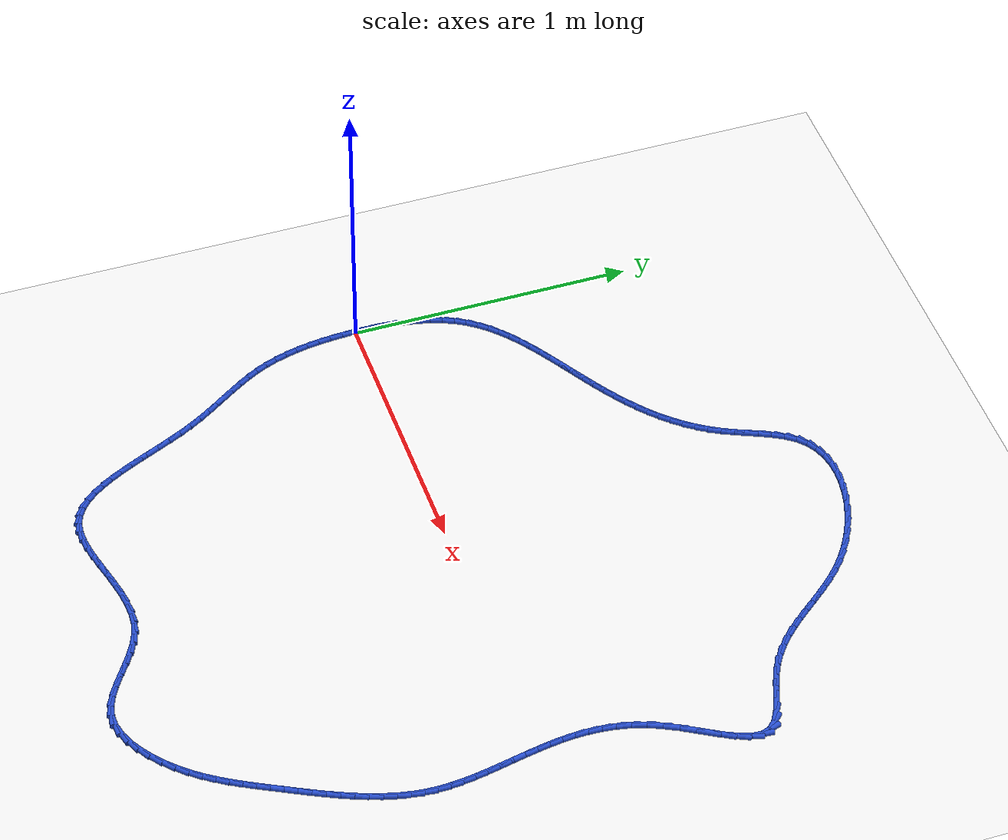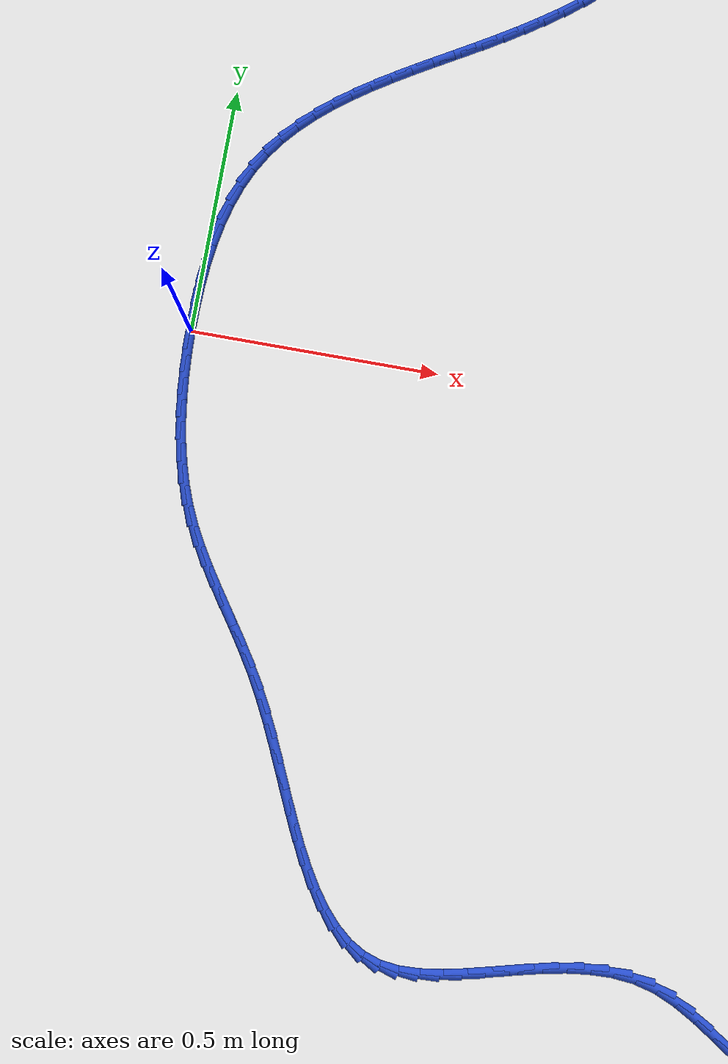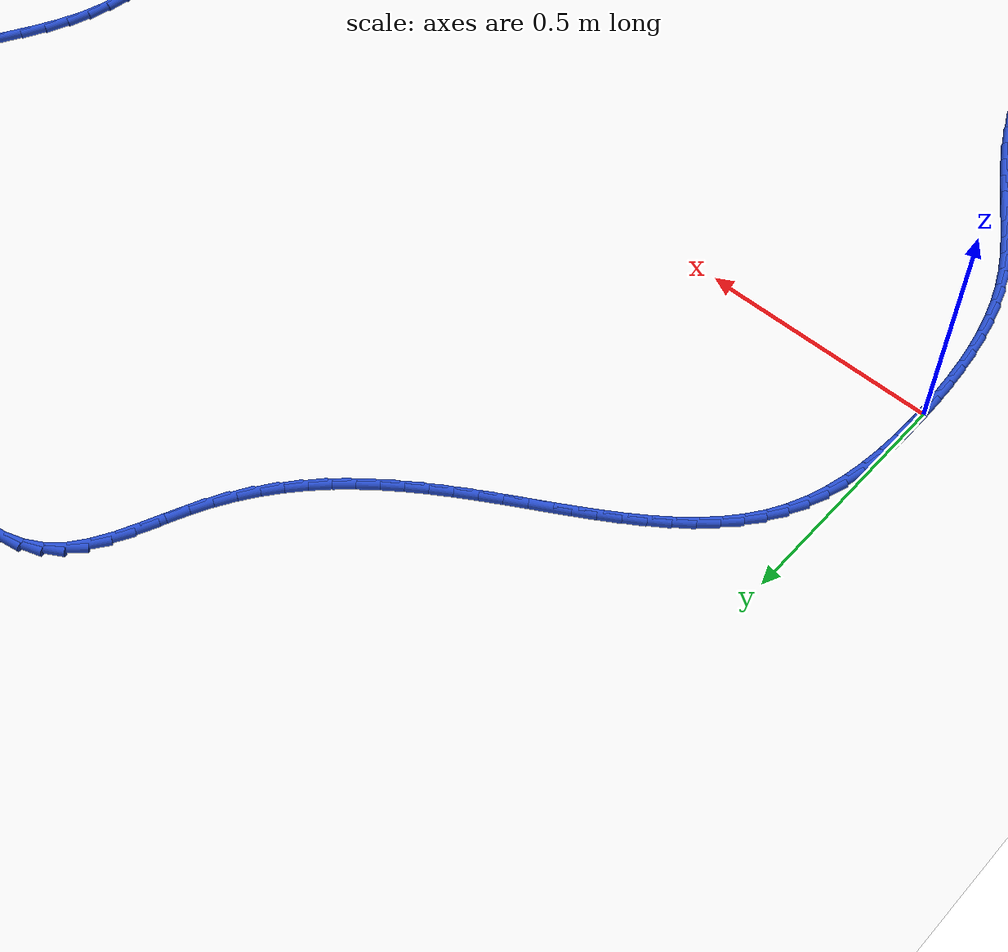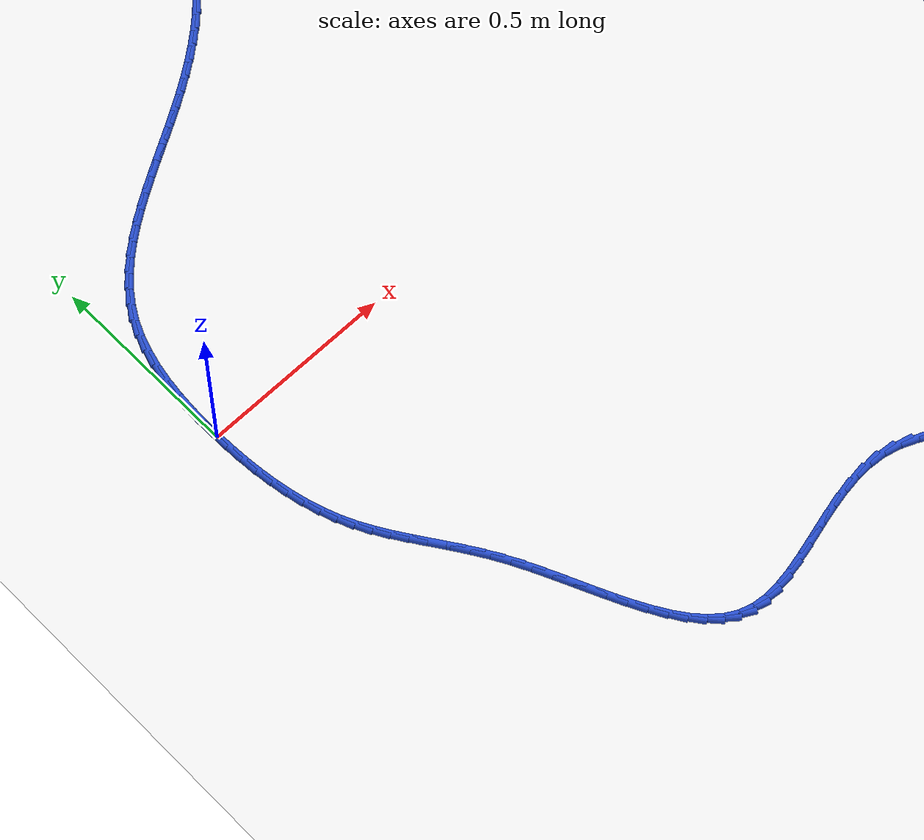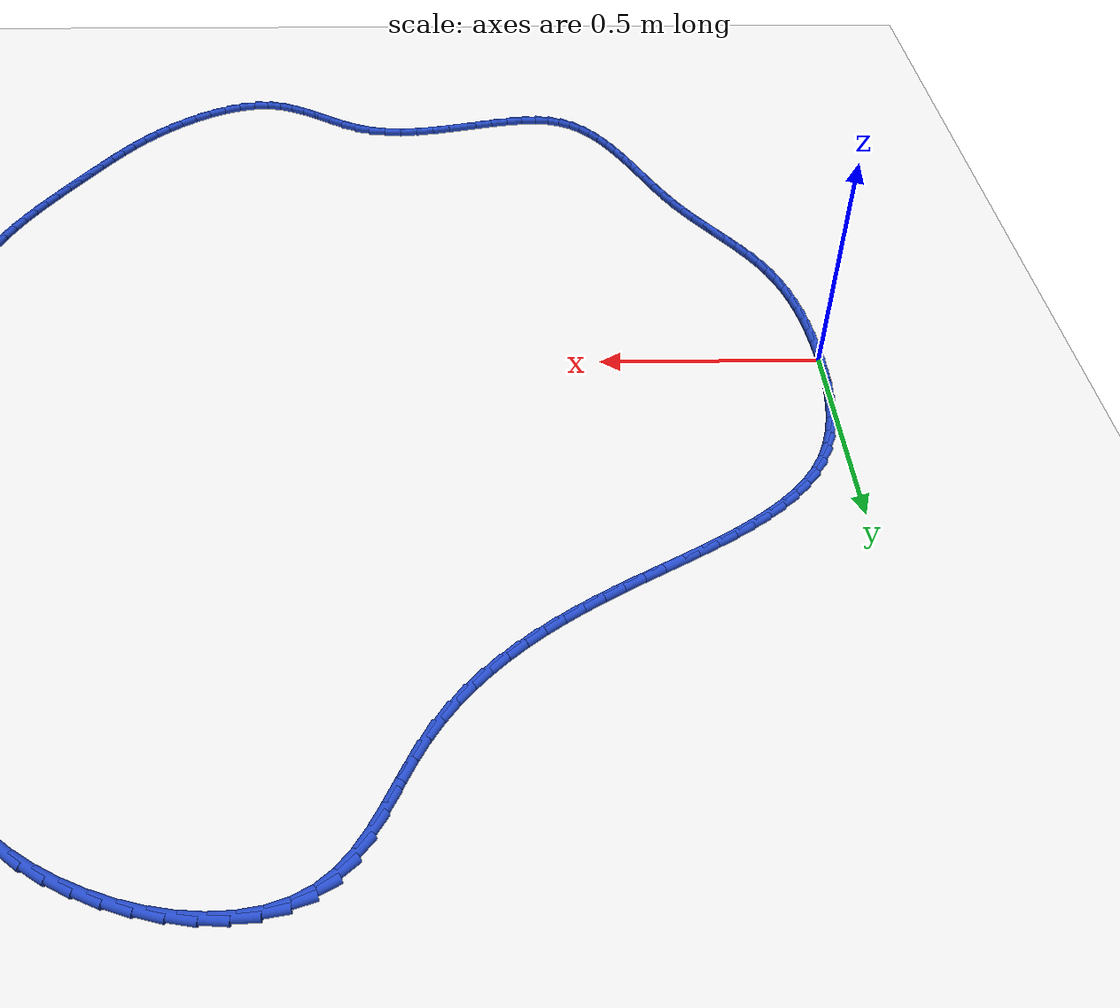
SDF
<sdf version="1.6">
 <world name="default">
  <light name="sun" type="directional">
   <pose>0 0 10 0 -0 0</pose>
   <diffuse>0.8 0.8 0.8 1</diffuse>
   <specular>0.2 0.2 0.2 1</specular>
   <attenuation>
    <range>1000</range>
    <constant>0.9</constant>
    <linear>0.01</linear>
    <quadratic>0.001</quadratic>
   </attenuation>
   <direction>-0.5 0.1 -0.9</direction>
  </light>
  <model name="ground_plane">
   <static>1</static>
   <link name="link">
    <collision name="collision">
     <geometry><plane><normal>0 0 1</normal><size>100 100</size></plane></geometry>
     <surface><friction><ode><mu>100</mu><mu2>50</mu2></ode></friction></surface>
    </collision>
    <visual name="visual">
     <cast_shadows>0</cast_shadows>
     <geometry><plane><normal>0 0 1</normal><size>100 100</size></plane></geometry>
     <material>
      <script><uri>file://media/materials/scripts/gazebo.material</uri><name>Gazebo/WhiteGlow</name></script>
     </material>
    </visual>
   </link>
  </model>
  <gravity>0 0 -9.8</gravity>
  <magnetic_field>6e-06 2.3e-05 -4.2e-05</magnetic_field>
  <atmosphere type="adiabatic"/>
  <physics name="default_physics" default="0" type="ode">
   <max_step_size>0.001</max_step_size>
   <real_time_factor>1</real_time_factor>
   <real_time_update_rate>1000</real_time_update_rate>
  </physics>
  <scene><ambient>0.4 0.4 0.4 1</ambient><background>0.7 0.7 0.7 1</background><shadows>1</shadows></scene>
  <spherical_coordinates>
   <surface_model>EARTH_WGS84</surface_model>
   <latitude_deg>0</latitude_deg>
   <longitude_deg>0</longitude_deg>
   <elevation>0</elevation>
   <heading_deg>0</heading_deg>
  </spherical_coordinates>
  <model name="line">
   <link name="link_0">
    <pose>1.474514954580286e-17 -1.3877787807814457e-17 0.01 0 1.57 -1.569611502420711</pose>
    <collision name="collision">
     <geometry><cylinder><radius>0.01</radius><length>0.08</length></cylinder></geometry>
    </collision>
    <visual name="visual">
     <material>
      <script><name>Gazebo/Blue</name><uri>file://media/materials/scripts/gazebo.material</uri></script>
     </material>
     <geometry><cylinder><radius>0.01</radius><length>0.08</length></cylinder></geometry>
    </visual>
   </link>
   <link name="link_1">
    <pose>-5.461354444209526e-05 0.04609418921178743 0.01 0 1.57 1.5378651562185328</pose>
    <collision name="collision">
     <geometry><cylinder><radius>0.01</radius><length>0.08</length></cylinder></geometry>
    </collision>
    <visual name="visual">
     <material>
      <script><name>Gazebo/Blue</name><uri>file://media/materials/scripts/gazebo.material</uri></script>
     </material>
     <geometry><cylinder><radius>0.01</radius><length>0.08</length></cylinder></geometry>
    </visual>
   </link>
   <link name="link_2">
    <pose>0.001460553691353006 0.09208767975349447 0.01 0 1.57 1.496667337225599</pose>
    <collision name="collision">
     <geometry><cylinder><radius>0.01</radius><length>0.08</length></cylinder></geometry>
    </collision>
    <visual name="visual">
     <material>
      <script><name>Gazebo/Blue</name><uri>file://media/materials/scripts/gazebo.material</uri></script>
     </material>
     <geometry><cylinder><radius>0.01</radius><length>0.08</length></cylinder></geometry>
    </visual>
   </link>
   <link name="link_3">
    <pose>0.004844474672389647 0.13765312442916 0.01 0 1.57 1.4475315382193203</pose>
    <collision name="collision">
     <geometry><cylinder><radius>0.01</radius><length>0.08</length></cylinder></geometry>
    </collision>
    <visual name="visual">
     <material>
      <script><name>Gazebo/Blue</name><uri>file://media/materials/scripts/gazebo.material</uri></script>
     </material>
     <geometry><cylinder><radius>0.01</radius><length>0.08</length></cylinder></geometry>
    </visual>
   </link>
   <link name="link_4">
    <pose>0.010396122363672163 0.1824631760428229 0.01 0 1.57 1.3894395232690393</pose>
    <collision name="collision">
     <geometry><cylinder><radius>0.01</radius><length>0.08</length></cylinder></geometry>
    </collision>
    <visual name="visual">
     <material>
      <script><name>Gazebo/Blue</name><uri>file://media/materials/scripts/gazebo.material</uri></script>
     </material>
     <geometry><cylinder><radius>0.01</radius><length>0.08</length></cylinder></geometry>
    </visual>
   </link>
   <link name="link_5">
    <pose>0.018414469730204885 0.2261904873985221 0.01 0 1.57 1.3212698312868223</pose>
    <collision name="collision">
     <geometry><cylinder><radius>0.01</radius><length>0.08</length></cylinder></geometry>
    </collision>
    <visual name="visual">
     <material>
      <script><name>Gazebo/Blue</name><uri>file://media/materials/scripts/gazebo.material</uri></script>
     </material>
     <geometry><cylinder><radius>0.01</radius><length>0.08</length></cylinder></geometry>
    </visual>
   </link>
   <link name="link_6">
    <pose>0.029198489736992145 0.2685077113002964 0.01 0 1.57 1.241919839483153</pose>
    <collision name="collision">
     <geometry><cylinder><radius>0.01</radius><length>0.08</length></cylinder></geometry>
    </collision>
    <visual name="visual">
     <material>
      <script><name>Gazebo/Blue</name><uri>file://media/materials/scripts/gazebo.material</uri></script>
     </material>
     <geometry><cylinder><radius>0.01</radius><length>0.08</length></cylinder></geometry>
    </visual>
   </link>
   <link name="link_7">
    <pose>0.043047155349038274 0.3090875005521847 0.01 0 1.57 1.1505249234120345</pose>
    <collision name="collision">
     <geometry><cylinder><radius>0.01</radius><length>0.08</length></cylinder></geometry>
    </collision>
    <visual name="visual">
     <material>
      <script><name>Gazebo/Blue</name><uri>file://media/materials/scripts/gazebo.material</uri></script>
     </material>
     <geometry><cylinder><radius>0.01</radius><length>0.08</length></cylinder></geometry>
    </visual>
   </link>
   <link name="link_8">
    <pose>0.06025943953134761 0.3476025079582259 0.01 0 1.57 1.047654850337171</pose>
    <collision name="collision">
     <geometry><cylinder><radius>0.01</radius><length>0.08</length></cylinder></geometry>
    </collision>
    <visual name="visual">
     <material>
      <script><name>Gazebo/Blue</name><uri>file://media/materials/scripts/gazebo.material</uri></script>
     </material>
     <geometry><cylinder><radius>0.01</radius><length>0.08</length></cylinder></geometry>
    </visual>
   </link>
   <link name="link_9">
    <pose>0.08110669816775862 0.3837491830798641 0.01 0 1.57 0.9456619193685916</pose>
    <collision name="collision">
     <geometry><cylinder><radius>0.01</radius><length>0.08</length></cylinder></geometry>
    </collision>
    <visual name="visual">
     <material>
      <script><name>Gazebo/Blue</name><uri>file://media/materials/scripts/gazebo.material</uri></script>
     </material>
     <geometry><cylinder><radius>0.01</radius><length>0.08</length></cylinder></geometry>
    </visual>
   </link>
   <link name="link_10">
    <pose>0.10549329707692662 0.4175401991047393 0.01 0 1.57 0.8545430566858977</pose>
    <collision name="collision">
     <geometry><cylinder><radius>0.01</radius><length>0.08</length></cylinder></geometry>
    </collision>
    <visual name="visual">
     <material>
      <script><name>Gazebo/Blue</name><uri>file://media/materials/scripts/gazebo.material</uri></script>
     </material>
     <geometry><cylinder><radius>0.01</radius><length>0.08</length></cylinder></geometry>
    </visual>
   </link>
   <link name="link_11">
    <pose>0.13306302004227455 0.44921276444343244 0.01 0 1.57 0.7755130728796676</pose>
    <collision name="collision">
     <geometry><cylinder><radius>0.01</radius><length>0.08</length></cylinder></geometry>
    </collision>
    <visual name="visual">
     <material>
      <script><name>Gazebo/Blue</name><uri>file://media/materials/scripts/gazebo.material</uri></script>
     </material>
     <geometry><cylinder><radius>0.01</radius><length>0.08</length></cylinder></geometry>
    </visual>
   </link>
   <link name="link_12">
    <pose>0.16345410067431382 0.47900886991338126 0.01 0 1.57 0.7086950156455445</pose>
    <collision name="collision">
     <geometry><cylinder><radius>0.01</radius><length>0.08</length></cylinder></geometry>
    </collision>
    <visual name="visual">
     <material>
      <script><name>Gazebo/Blue</name><uri>file://media/materials/scripts/gazebo.material</uri></script>
     </material>
     <geometry><cylinder><radius>0.01</radius><length>0.08</length></cylinder></geometry>
    </visual>
   </link>
   <link name="link_13">
    <pose>0.19630477258355566 0.5071705063320233 0.01 0 1.57 0.653637642707787</pose>
    <collision name="collision">
     <geometry><cylinder><radius>0.01</radius><length>0.08</length></cylinder></geometry>
    </collision>
    <visual name="visual">
     <material>
      <script><name>Gazebo/Blue</name><uri>file://media/materials/scripts/gazebo.material</uri></script>
     </material>
     <geometry><cylinder><radius>0.01</radius><length>0.08</length></cylinder></geometry>
    </visual>
   </link>
   <link name="link_14">
    <pose>0.23125326938051127 0.533939664516796 0.01 0 1.57 0.6096179353655401</pose>
    <collision name="collision">
     <geometry><cylinder><radius>0.01</radius><length>0.08</length></cylinder></geometry>
    </collision>
    <visual name="visual">
     <material>
      <script><name>Gazebo/Blue</name><uri>file://media/materials/scripts/gazebo.material</uri></script>
     </material>
     <geometry><cylinder><radius>0.01</radius><length>0.08</length></cylinder></geometry>
    </visual>
   </link>
   <link name="link_15">
    <pose>0.26793782467569227 0.5595583352851373 0.01 0 1.57 0.5758564400715441</pose>
    <collision name="collision">
     <geometry><cylinder><radius>0.01</radius><length>0.08</length></cylinder></geometry>
    </collision>
    <visual name="visual">
     <material>
      <script><name>Gazebo/Blue</name><uri>file://media/materials/scripts/gazebo.material</uri></script>
     </material>
     <geometry><cylinder><radius>0.01</radius><length>0.08</length></cylinder></geometry>
    </visual>
   </link>
   <link name="link_16">
    <pose>0.30599667207960984 0.5842685094544845 0.01 0 1.57 0.5516502759008736</pose>
    <collision name="collision">
     <geometry><cylinder><radius>0.01</radius><length>0.08</length></cylinder></geometry>
    </collision>
    <visual name="visual">
     <material>
      <script><name>Gazebo/Blue</name><uri>file://media/materials/scripts/gazebo.material</uri></script>
     </material>
     <geometry><cylinder><radius>0.01</radius><length>0.08</length></cylinder></geometry>
    </visual>
   </link>
   <link name="link_17">
    <pose>0.3450680452027752 0.6083121778422756 0.01 0 1.57 0.536446397267386</pose>
    <collision name="collision">
     <geometry><cylinder><radius>0.01</radius><length>0.08</length></cylinder></geometry>
    </collision>
    <visual name="visual">
     <material>
      <script><name>Gazebo/Blue</name><uri>file://media/materials/scripts/gazebo.material</uri></script>
     </material>
     <geometry><cylinder><radius>0.01</radius><length>0.08</length></cylinder></geometry>
    </visual>
   </link>
   <link name="link_18">
    <pose>0.38479017765569967 0.6319313312659477 0.01 0 1.57 0.5298777556419644</pose>
    <collision name="collision">
     <geometry><cylinder><radius>0.01</radius><length>0.08</length></cylinder></geometry>
    </collision>
    <visual name="visual">
     <material>
      <script><name>Gazebo/Blue</name><uri>file://media/materials/scripts/gazebo.material</uri></script>
     </material>
     <geometry><cylinder><radius>0.01</radius><length>0.08</length></cylinder></geometry>
    </visual>
   </link>
   <link name="link_19">
    <pose>0.42480130304889463 0.6553679605429387 0.01 0 1.57 0.5317788992559888</pose>
    <collision name="collision">
     <geometry><cylinder><radius>0.01</radius><length>0.08</length></cylinder></geometry>
    </collision>
    <visual name="visual">
     <material>
      <script><name>Gazebo/Blue</name><uri>file://media/materials/scripts/gazebo.material</uri></script>
     </material>
     <geometry><cylinder><radius>0.01</radius><length>0.08</length></cylinder></geometry>
    </visual>
   </link>
   <link name="link_20">
    <pose>0.4647396549928715 0.6788640564906863 0.01 0 1.57 0.5421908264301276</pose>
    <collision name="collision">
     <geometry><cylinder><radius>0.01</radius><length>0.08</length></cylinder></geometry>
    </collision>
    <visual name="visual">
     <material>
      <script><name>Gazebo/Blue</name><uri>file://media/materials/scripts/gazebo.material</uri></script>
     </material>
     <geometry><cylinder><radius>0.01</radius><length>0.08</length></cylinder></geometry>
    </visual>
   </link>
   <link name="link_21">
    <pose>0.5042434670981417 0.7026616099266283 0.01 0 1.57 0.5609635225614444</pose>
    <collision name="collision">
     <geometry><cylinder><radius>0.01</radius><length>0.08</length></cylinder></geometry>
    </collision>
    <visual name="visual">
     <material>
      <script><name>Gazebo/Blue</name><uri>file://media/materials/scripts/gazebo.material</uri></script>
     </material>
     <geometry><cylinder><radius>0.01</radius><length>0.08</length></cylinder></geometry>
    </visual>
   </link>
   <link name="link_22">
    <pose>0.5429727379642396 0.7269949241003821 0.01 0 1.57 0.5858534026313756</pose>
    <collision name="collision">
     <geometry><cylinder><radius>0.01</radius><length>0.08</length></cylinder></geometry>
    </collision>
    <visual name="visual">
     <material>
      <script><name>Gazebo/Blue</name><uri>file://media/materials/scripts/gazebo.material</uri></script>
     </material>
     <geometry><cylinder><radius>0.01</radius><length>0.08</length></cylinder></geometry>
    </visual>
   </link>
   <link name="link_23">
    <pose>0.5807285957842947 0.7520484541628164 0.01 0 1.57 0.6160258993603437</pose>
    <collision name="collision">
     <geometry><cylinder><radius>0.01</radius><length>0.08</length></cylinder></geometry>
    </collision>
    <visual name="visual">
     <material>
      <script><name>Gazebo/Blue</name><uri>file://media/materials/scripts/gazebo.material</uri></script>
     </material>
     <geometry><cylinder><radius>0.01</radius><length>0.08</length></cylinder></geometry>
    </visual>
   </link>
   <link name="link_24">
    <pose>0.617368452465538 0.7779867754078025 0.01 0 1.57 0.6516195660069333</pose>
    <collision name="collision">
     <geometry><cylinder><radius>0.01</radius><length>0.08</length></cylinder></geometry>
    </collision>
    <visual name="visual">
     <material>
      <script><name>Gazebo/Blue</name><uri>file://media/materials/scripts/gazebo.material</uri></script>
     </material>
     <geometry><cylinder><radius>0.01</radius><length>0.08</length></cylinder></geometry>
    </visual>
   </link>
   <link name="link_25">
    <pose>0.6527498660742618 0.8049744115046663 0.01 0 1.57 0.69272663981271</pose>
    <collision name="collision">
     <geometry><cylinder><radius>0.01</radius><length>0.08</length></cylinder></geometry>
    </collision>
    <visual name="visual">
     <material>
      <script><name>Gazebo/Blue</name><uri>file://media/materials/scripts/gazebo.material</uri></script>
     </material>
     <geometry><cylinder><radius>0.01</radius><length>0.08</length></cylinder></geometry>
    </visual>
   </link>
   <link name="link_26">
    <pose>0.6867303946767578 0.8331758861227329 0.01 0 1.57 0.7393568556690804</pose>
    <collision name="collision">
     <geometry><cylinder><radius>0.01</radius><length>0.08</length></cylinder></geometry>
    </collision>
    <visual name="visual">
     <material>
      <script><name>Gazebo/Blue</name><uri>file://media/materials/scripts/gazebo.material</uri></script>
     </material>
     <geometry><cylinder><radius>0.01</radius><length>0.08</length></cylinder></geometry>
    </visual>
   </link>
   <link name="link_27">
    <pose>0.7191675963393177 0.8627557229313279 0.01 0 1.57 0.7913988177955018</pose>
    <collision name="collision">
     <geometry><cylinder><radius>0.01</radius><length>0.08</length></cylinder></geometry>
    </collision>
    <visual name="visual">
     <material>
      <script><name>Gazebo/Blue</name><uri>file://media/materials/scripts/gazebo.material</uri></script>
     </material>
     <geometry><cylinder><radius>0.01</radius><length>0.08</length></cylinder></geometry>
    </visual>
   </link>
   <link name="link_28">
    <pose>0.7499190291282343 0.8938784455997767 0.01 0 1.57 0.8485803193854166</pose>
    <collision name="collision">
     <geometry><cylinder><radius>0.01</radius><length>0.08</length></cylinder></geometry>
    </collision>
    <visual name="visual">
     <material>
      <script><name>Gazebo/Blue</name><uri>file://media/materials/scripts/gazebo.material</uri></script>
     </material>
     <geometry><cylinder><radius>0.01</radius><length>0.08</length></cylinder></geometry>
    </visual>
   </link>
   <link name="link_29">
    <pose>0.7788422511097985 0.9267085777974045 0.01 0 1.57 0.9104344827017881</pose>
    <collision name="collision">
     <geometry><cylinder><radius>0.01</radius><length>0.08</length></cylinder></geometry>
    </collision>
    <visual name="visual">
     <material>
      <script><name>Gazebo/Blue</name><uri>file://media/materials/scripts/gazebo.material</uri></script>
     </material>
     <geometry><cylinder><radius>0.01</radius><length>0.08</length></cylinder></geometry>
    </visual>
   </link>
   <link name="link_30">
    <pose>0.805794820350303 0.9614106431935366 0.01 0 1.57 0.9762809017210619</pose>
    <collision name="collision">
     <geometry><cylinder><radius>0.01</radius><length>0.08</length></cylinder></geometry>
    </collision>
    <visual name="visual">
     <material>
      <script><name>Gazebo/Blue</name><uri>file://media/materials/scripts/gazebo.material</uri></script>
     </material>
     <geometry><cylinder><radius>0.01</radius><length>0.08</length></cylinder></geometry>
    </visual>
   </link>
   <link name="link_31">
    <pose>0.8306342949160396 0.9981491654574988 0.01 0 1.57 1.045231243875748</pose>
    <collision name="collision">
     <geometry><cylinder><radius>0.01</radius><length>0.08</length></cylinder></geometry>
    </collision>
    <visual name="visual">
     <material>
      <script><name>Gazebo/Blue</name><uri>file://media/materials/scripts/gazebo.material</uri></script>
     </material>
     <geometry><cylinder><radius>0.01</radius><length>0.08</length></cylinder></geometry>
    </visual>
   </link>
   <link name="link_32">
    <pose>0.8532182328733002 1.0370886682586165 0.01 0 1.57 1.1138030286405831</pose>
    <collision name="collision">
     <geometry><cylinder><radius>0.01</radius><length>0.08</length></cylinder></geometry>
    </collision>
    <visual name="visual">
     <material>
      <script><name>Gazebo/Blue</name><uri>file://media/materials/scripts/gazebo.material</uri></script>
     </material>
     <geometry><cylinder><radius>0.01</radius><length>0.08</length></cylinder></geometry>
    </visual>
   </link>
   <link name="link_33">
    <pose>0.8734820525060996 1.078299620335481 0.01 0 1.57 1.1571150702648454</pose>
    <collision name="collision">
     <geometry><cylinder><radius>0.01</radius><length>0.08</length></cylinder></geometry>
    </collision>
    <visual name="visual">
     <material>
      <script><name>Gazebo/Blue</name><uri>file://media/materials/scripts/gazebo.material</uri></script>
     </material>
     <geometry><cylinder><radius>0.01</radius><length>0.08</length></cylinder></geometry>
    </visual>
   </link>
   <link name="link_34">
    <pose>0.8921722653160781 1.1208726920311354 0.01 0 1.57 1.1628281830712808</pose>
    <collision name="collision">
     <geometry><cylinder><radius>0.01</radius><length>0.08</length></cylinder></geometry>
    </collision>
    <visual name="visual">
     <material>
      <script><name>Gazebo/Blue</name><uri>file://media/materials/scripts/gazebo.material</uri></script>
     </material>
     <geometry><cylinder><radius>0.01</radius><length>0.08</length></cylinder></geometry>
    </visual>
   </link>
   <link name="link_35">
    <pose>0.9105172241950978 1.1633164906029123 0.01 0 1.57 1.1304093988465822</pose>
    <collision name="collision">
     <geometry><cylinder><radius>0.01</radius><length>0.08</length></cylinder></geometry>
    </collision>
    <visual name="visual">
     <material>
      <script><name>Gazebo/Blue</name><uri>file://media/materials/scripts/gazebo.material</uri></script>
     </material>
     <geometry><cylinder><radius>0.01</radius><length>0.08</length></cylinder></geometry>
    </visual>
   </link>
   <link name="link_36">
    <pose>0.92975164044362 1.2041319423678944 0.01 0 1.57 1.0552064715295566</pose>
    <collision name="collision">
     <geometry><cylinder><radius>0.01</radius><length>0.08</length></cylinder></geometry>
    </collision>
    <visual name="visual">
     <material>
      <script><name>Gazebo/Blue</name><uri>file://media/materials/scripts/gazebo.material</uri></script>
     </material>
     <geometry><cylinder><radius>0.01</radius><length>0.08</length></cylinder></geometry>
    </visual>
   </link>
   <link name="link_37">
    <pose>0.951110225362104 1.2418199736431639 0.01 0 1.57 0.9288201876240286</pose>
    <collision name="collision">
     <geometry><cylinder><radius>0.01</radius><length>0.08</length></cylinder></geometry>
    </collision>
    <visual name="visual">
     <material>
      <script><name>Gazebo/Blue</name><uri>file://media/materials/scripts/gazebo.material</uri></script>
     </material>
     <geometry><cylinder><radius>0.01</radius><length>0.08</length></cylinder></geometry>
    </visual>
   </link>
   <link name="link_38">
    <pose>0.9758276902510103 1.2748815107458031 0.01 0 1.57 0.7437885615825935</pose>
    <collision name="collision">
     <geometry><cylinder><radius>0.01</radius><length>0.08</length></cylinder></geometry>
    </collision>
    <visual name="visual">
     <material>
      <script><name>Gazebo/Blue</name><uri>file://media/materials/scripts/gazebo.material</uri></script>
     </material>
     <geometry><cylinder><radius>0.01</radius><length>0.08</length></cylinder></geometry>
    </visual>
   </link>
   <link name="link_39">
    <pose>1.005121657326347 1.3018337441971113 0.01 0 1.57 0.5305552201940364</pose>
    <collision name="collision">
     <geometry><cylinder><radius>0.01</radius><length>0.08</length></cylinder></geometry>
    </collision>
    <visual name="visual">
     <material>
      <script><name>Gazebo/Blue</name><uri>file://media/materials/scripts/gazebo.material</uri></script>
     </material>
     <geometry><cylinder><radius>0.01</radius><length>0.08</length></cylinder></geometry>
    </visual>
   </link>
   <link name="link_40">
    <pose>1.0394136147600852 1.3219515696320194 0.01 0 1.57 0.3393083787846759</pose>
    <collision name="collision">
     <geometry><cylinder><radius>0.01</radius><length>0.08</length></cylinder></geometry>
    </collision>
    <visual name="visual">
     <material>
      <script><name>Gazebo/Blue</name><uri>file://media/materials/scripts/gazebo.material</uri></script>
     </material>
     <geometry><cylinder><radius>0.01</radius><length>0.08</length></cylinder></geometry>
    </visual>
   </link>
   <link name="link_41">
    <pose>1.0780073963664025 1.335573588513033 0.01 0 1.57 0.17725714844688686</pose>
    <collision name="collision">
     <geometry><cylinder><radius>0.01</radius><length>0.08</length></cylinder></geometry>
    </collision>
    <visual name="visual">
     <material>
      <script><name>Gazebo/Blue</name><uri>file://media/materials/scripts/gazebo.material</uri></script>
     </material>
     <geometry><cylinder><radius>0.01</radius><length>0.08</length></cylinder></geometry>
    </visual>
   </link>
   <link name="link_42">
    <pose>1.1201231142382877 1.3431180828247264 0.01 0 1.57 0.04200260265851956</pose>
    <collision name="collision">
     <geometry><cylinder><radius>0.01</radius><length>0.08</length></cylinder></geometry>
    </collision>
    <visual name="visual">
     <material>
      <script><name>Gazebo/Blue</name><uri>file://media/materials/scripts/gazebo.material</uri></script>
     </material>
     <geometry><cylinder><radius>0.01</radius><length>0.08</length></cylinder></geometry>
    </visual>
   </link>
   <link name="link_43">
    <pose>1.1649808804687278 1.3450033345516759 0.01 0 1.57 -0.07155031408301973</pose>
    <collision name="collision">
     <geometry><cylinder><radius>0.01</radius><length>0.08</length></cylinder></geometry>
    </collision>
    <visual name="visual">
     <material>
      <script><name>Gazebo/Blue</name><uri>file://media/materials/scripts/gazebo.material</uri></script>
     </material>
     <geometry><cylinder><radius>0.01</radius><length>0.08</length></cylinder></geometry>
    </visual>
   </link>
   <link name="link_44">
    <pose>1.2118008071507123 1.3416476256784562 0.01 0 1.57 -0.16875486050029517</pose>
    <collision name="collision">
     <geometry><cylinder><radius>0.01</radius><length>0.08</length></cylinder></geometry>
    </collision>
    <visual name="visual">
     <material>
      <script><name>Gazebo/Blue</name><uri>file://media/materials/scripts/gazebo.material</uri></script>
     </material>
     <geometry><cylinder><radius>0.01</radius><length>0.08</length></cylinder></geometry>
    </visual>
   </link>
   <link name="link_45">
    <pose>1.2598030063772294 1.3334692381896442 0.01 0 1.57 -0.25432146671569417</pose>
    <collision name="collision">
     <geometry><cylinder><radius>0.01</radius><length>0.08</length></cylinder></geometry>
    </collision>
    <visual name="visual">
     <material>
      <script><name>Gazebo/Blue</name><uri>file://media/materials/scripts/gazebo.material</uri></script>
     </material>
     <geometry><cylinder><radius>0.01</radius><length>0.08</length></cylinder></geometry>
    </visual>
   </link>
   <link name="link_46">
    <pose>1.308207590241266 1.3208864540698144 0.01 0 1.57 -0.33220528853665615</pose>
    <collision name="collision">
     <geometry><cylinder><radius>0.01</radius><length>0.08</length></cylinder></geometry>
    </collision>
    <visual name="visual">
     <material>
      <script><name>Gazebo/Blue</name><uri>file://media/materials/scripts/gazebo.material</uri></script>
     </material>
     <geometry><cylinder><radius>0.01</radius><length>0.08</length></cylinder></geometry>
    </visual>
   </link>
   <link name="link_47">
    <pose>1.356234670835812 1.3043175553035422 0.01 0 1.57 -0.40578767669279425</pose>
    <collision name="collision">
     <geometry><cylinder><radius>0.01</radius><length>0.08</length></cylinder></geometry>
    </collision>
    <visual name="visual">
     <material>
      <script><name>Gazebo/Blue</name><uri>file://media/materials/scripts/gazebo.material</uri></script>
     </material>
     <geometry><cylinder><radius>0.01</radius><length>0.08</length></cylinder></geometry>
    </visual>
   </link>
   <link name="link_48">
    <pose>1.4031043602538542 1.2841808238754042 0.01 0 1.57 -0.4781418470452831</pose>
    <collision name="collision">
     <geometry><cylinder><radius>0.01</radius><length>0.08</length></cylinder></geometry>
    </collision>
    <visual name="visual">
     <material>
      <script><name>Gazebo/Blue</name><uri>file://media/materials/scripts/gazebo.material</uri></script>
     </material>
     <geometry><cylinder><radius>0.01</radius><length>0.08</length></cylinder></geometry>
    </visual>
   </link>
   <link name="link_49">
    <pose>1.4480367705883816 1.2608945417699748 0.01 0 1.57 -0.5523237469019905</pose>
    <collision name="collision">
     <geometry><cylinder><radius>0.01</radius><length>0.08</length></cylinder></geometry>
    </collision>
    <visual name="visual">
     <material>
      <script><name>Gazebo/Blue</name><uri>file://media/materials/scripts/gazebo.material</uri></script>
     </material>
     <geometry><cylinder><radius>0.01</radius><length>0.08</length></cylinder></geometry>
    </visual>
   </link>
   <link name="link_50">
    <pose>1.4902520139323825 1.2348769909718302 0.01 0 1.57 -0.6314818254677969</pose>
    <collision name="collision">
     <geometry><cylinder><radius>0.01</radius><length>0.08</length></cylinder></geometry>
    </collision>
    <visual name="visual">
     <material>
      <script><name>Gazebo/Blue</name><uri>file://media/materials/scripts/gazebo.material</uri></script>
     </material>
     <geometry><cylinder><radius>0.01</radius><length>0.08</length></cylinder></geometry>
    </visual>
   </link>
   <link name="link_51">
    <pose>1.5289875393612393 1.2065463404608834 0.01 0 1.57 -0.7108495834030777</pose>
    <collision name="collision">
     <geometry><cylinder><radius>0.01</radius><length>0.08</length></cylinder></geometry>
    </collision>
    <visual name="visual">
     <material>
      <script><name>Gazebo/Blue</name><uri>file://media/materials/scripts/gazebo.material</uri></script>
     </material>
     <geometry><cylinder><radius>0.01</radius><length>0.08</length></cylinder></geometry>
    </visual>
   </link>
   <link name="link_52">
    <pose>1.564097124812674 1.1763167419069183 0.01 0 1.57 -0.7793377984106841</pose>
    <collision name="collision">
     <geometry><cylinder><radius>0.01</radius><length>0.08</length></cylinder></geometry>
    </collision>
    <visual name="visual">
     <material>
      <script><name>Gazebo/Blue</name><uri>file://media/materials/scripts/gazebo.material</uri></script>
     </material>
     <geometry><cylinder><radius>0.01</radius><length>0.08</length></cylinder></geometry>
    </visual>
   </link>
   <link name="link_53">
    <pose>1.5962033421453654 1.144597335882893 0.01 0 1.57 -0.8337298446864628</pose>
    <collision name="collision">
     <geometry><cylinder><radius>0.01</radius><length>0.08</length></cylinder></geometry>
    </collision>
    <visual name="visual">
     <material>
      <script><name>Gazebo/Blue</name><uri>file://media/materials/scripts/gazebo.material</uri></script>
     </material>
     <geometry><cylinder><radius>0.01</radius><length>0.08</length></cylinder></geometry>
    </visual>
   </link>
   <link name="link_54">
    <pose>1.6259770610161821 1.1117969481505565 0.01 0 1.57 -0.8722214014372216</pose>
    <collision name="collision">
     <geometry><cylinder><radius>0.01</radius><length>0.08</length></cylinder></geometry>
    </collision>
    <visual name="visual">
     <material>
      <script><name>Gazebo/Blue</name><uri>file://media/materials/scripts/gazebo.material</uri></script>
     </material>
     <geometry><cylinder><radius>0.01</radius><length>0.08</length></cylinder></geometry>
    </visual>
   </link>
   <link name="link_55">
    <pose>1.6540891510819917 1.0783244044716571 0.01 0 1.57 -0.8936627354179378</pose>
    <collision name="collision">
     <geometry><cylinder><radius>0.01</radius><length>0.08</length></cylinder></geometry>
    </collision>
    <visual name="visual">
     <material>
      <script><name>Gazebo/Blue</name><uri>file://media/materials/scripts/gazebo.material</uri></script>
     </material>
     <geometry><cylinder><radius>0.01</radius><length>0.08</length></cylinder></geometry>
    </visual>
   </link>
   <link name="link_56">
    <pose>1.6812104819996632 1.044588530607946 0.01 0 1.57 -0.897343031162592</pose>
    <collision name="collision">
     <geometry><cylinder><radius>0.01</radius><length>0.08</length></cylinder></geometry>
    </collision>
    <visual name="visual">
     <material>
      <script><name>Gazebo/Blue</name><uri>file://media/materials/scripts/gazebo.material</uri></script>
     </material>
     <geometry><cylinder><radius>0.01</radius><length>0.08</length></cylinder></geometry>
    </visual>
   </link>
   <link name="link_57">
    <pose>1.7080119234260651 1.0109981523211715 0.01 0 1.57 -0.8828420824173352</pose>
    <collision name="collision">
     <geometry><cylinder><radius>0.01</radius><length>0.08</length></cylinder></geometry>
    </collision>
    <visual name="visual">
     <material>
      <script><name>Gazebo/Blue</name><uri>file://media/materials/scripts/gazebo.material</uri></script>
     </material>
     <geometry><cylinder><radius>0.01</radius><length>0.08</length></cylinder></geometry>
    </visual>
   </link>
   <link name="link_58">
    <pose>1.735164345018065 0.9779620953730824 0.01 0 1.57 -0.8500187840394143</pose>
    <collision name="collision">
     <geometry><cylinder><radius>0.01</radius><length>0.08</length></cylinder></geometry>
    </collision>
    <visual name="visual">
     <material>
      <script><name>Gazebo/Blue</name><uri>file://media/materials/scripts/gazebo.material</uri></script>
     </material>
     <geometry><cylinder><radius>0.01</radius><length>0.08</length></cylinder></geometry>
    </visual>
   </link>
   <link name="link_59">
    <pose>1.763338616432532 0.9458891855254293 0.01 0 1.57 -0.7991660670928029</pose>
    <collision name="collision">
     <geometry><cylinder><radius>0.01</radius><length>0.08</length></cylinder></geometry>
    </collision>
    <visual name="visual">
     <material>
      <script><name>Gazebo/Blue</name><uri>file://media/materials/scripts/gazebo.material</uri></script>
     </material>
     <geometry><cylinder><radius>0.01</radius><length>0.08</length></cylinder></geometry>
    </visual>
   </link>
   <link name="link_60">
    <pose>1.793205607326334 0.9151882485399607 0.01 0 1.57 -0.7313151782882586</pose>
    <collision name="collision">
     <geometry><cylinder><radius>0.01</radius><length>0.08</length></cylinder></geometry>
    </collision>
    <visual name="visual">
     <material>
      <script><name>Gazebo/Blue</name><uri>file://media/materials/scripts/gazebo.material</uri></script>
     </material>
     <geometry><cylinder><radius>0.01</radius><length>0.08</length></cylinder></geometry>
    </visual>
   </link>
   <link name="link_61">
    <pose>1.8254361873563405 0.8862681101784261 0.01 0 1.57 -0.6485945372411348</pose>
    <collision name="collision">
     <geometry><cylinder><radius>0.01</radius><length>0.08</length></cylinder></geometry>
    </collision>
    <visual name="visual">
     <material>
      <script><name>Gazebo/Blue</name><uri>file://media/materials/scripts/gazebo.material</uri></script>
     </material>
     <geometry><cylinder><radius>0.01</radius><length>0.08</length></cylinder></geometry>
    </visual>
   </link>
   <link name="link_62">
    <pose>1.860701226179418 0.8595375962025746 0.01 0 1.57 -0.5544475603398086</pose>
    <collision name="collision">
     <geometry><cylinder><radius>0.01</radius><length>0.08</length></cylinder></geometry>
    </collision>
    <visual name="visual">
     <material>
      <script><name>Gazebo/Blue</name><uri>file://media/materials/scripts/gazebo.material</uri></script>
     </material>
     <geometry><cylinder><radius>0.01</radius><length>0.08</length></cylinder></geometry>
    </visual>
   </link>
   <link name="link_63">
    <pose>1.8996715934524364 0.8354055323741557 0.01 0 1.57 -0.45410261676943225</pose>
    <collision name="collision">
     <geometry><cylinder><radius>0.01</radius><length>0.08</length></cylinder></geometry>
    </collision>
    <visual name="visual">
     <material>
      <script><name>Gazebo/Blue</name><uri>file://media/materials/scripts/gazebo.material</uri></script>
     </material>
     <geometry><cylinder><radius>0.01</radius><length>0.08</length></cylinder></geometry>
    </visual>
   </link>
   <link name="link_64">
    <pose>1.9429829982231206 0.8142641497965635 0.01 0 1.57 -0.3791846506475868</pose>
    <collision name="collision">
     <geometry><cylinder><radius>0.01</radius><length>0.08</length></cylinder></geometry>
    </collision>
    <visual name="visual">
     <material>
      <script><name>Gazebo/Blue</name><uri>file://media/materials/scripts/gazebo.material</uri></script>
     </material>
     <geometry><cylinder><radius>0.01</radius><length>0.08</length></cylinder></geometry>
    </visual>
   </link>
   <link name="link_65">
    <pose>1.98956764038835 0.7957016789300416 0.01 0 1.57 -0.3617420133453219</pose>
    <collision name="collision">
     <geometry><cylinder><radius>0.01</radius><length>0.08</length></cylinder></geometry>
    </collision>
    <visual name="visual">
     <material>
      <script><name>Gazebo/Blue</name><uri>file://media/materials/scripts/gazebo.material</uri></script>
     </material>
     <geometry><cylinder><radius>0.01</radius><length>0.08</length></cylinder></geometry>
    </visual>
   </link>
   <link name="link_66">
    <pose>2.0359275795647616 0.7781594034472076 0.01 0 1.57 -0.4044022111047707</pose>
    <collision name="collision">
     <geometry><cylinder><radius>0.01</radius><length>0.08</length></cylinder></geometry>
    </collision>
    <visual name="visual">
     <material>
      <script><name>Gazebo/Blue</name><uri>file://media/materials/scripts/gazebo.material</uri></script>
     </material>
     <geometry><cylinder><radius>0.01</radius><length>0.08</length></cylinder></geometry>
    </visual>
   </link>
   <link name="link_67">
    <pose>2.078378614364323 0.7599906979140717 0.01 0 1.57 -0.5303823493370992</pose>
    <collision name="collision">
     <geometry><cylinder><radius>0.01</radius><length>0.08</length></cylinder></geometry>
    </collision>
    <visual name="visual">
     <material>
      <script><name>Gazebo/Blue</name><uri>file://media/materials/scripts/gazebo.material</uri></script>
     </material>
     <geometry><cylinder><radius>0.01</radius><length>0.08</length></cylinder></geometry>
    </visual>
   </link>
   <link name="link_68">
    <pose>2.1132365433989984 0.7395489368966425 0.01 0 1.57 -0.801683466181444</pose>
    <collision name="collision">
     <geometry><cylinder><radius>0.01</radius><length>0.08</length></cylinder></geometry>
    </collision>
    <visual name="visual">
     <material>
      <script><name>Gazebo/Blue</name><uri>file://media/materials/scripts/gazebo.material</uri></script>
     </material>
     <geometry><cylinder><radius>0.01</radius><length>0.08</length></cylinder></geometry>
    </visual>
   </link>
   <link name="link_69">
    <pose>2.1368171652807546 0.7151874949609303 0.01 0 1.57 -1.2546153297272837</pose>
    <collision name="collision">
     <geometry><cylinder><radius>0.01</radius><length>0.08</length></cylinder></geometry>
    </collision>
    <visual name="visual">
     <material>
      <script><name>Gazebo/Blue</name><uri>file://media/materials/scripts/gazebo.material</uri></script>
     </material>
     <geometry><cylinder><radius>0.01</radius><length>0.08</length></cylinder></geometry>
    </visual>
   </link>
   <link name="link_70">
    <pose>2.1464769208990937 0.6856610746130942 0.01 0 1.57 1.491147452122521</pose>
    <collision name="collision">
     <geometry><cylinder><radius>0.01</radius><length>0.08</length></cylinder></geometry>
    </collision>
    <visual name="visual">
     <material>
      <script><name>Gazebo/Blue</name><uri>file://media/materials/scripts/gazebo.material</uri></script>
     </material>
     <geometry><cylinder><radius>0.01</radius><length>0.08</length></cylinder></geometry>
    </visual>
   </link>
   <link name="link_71">
    <pose>2.1437367263078873 0.6513304251974817 0.01 0 1.57 1.2540540255600008</pose>
    <collision name="collision">
     <geometry><cylinder><radius>0.01</radius><length>0.08</length></cylinder></geometry>
    </collision>
    <visual name="visual">
     <material>
      <script><name>Gazebo/Blue</name><uri>file://media/materials/scripts/gazebo.material</uri></script>
     </material>
     <geometry><cylinder><radius>0.01</radius><length>0.08</length></cylinder></geometry>
    </visual>
   </link>
   <link name="link_72">
    <pose>2.131159093083825 0.6129579916215243 0.01 0 1.57 1.1260174141696433</pose>
    <collision name="collision">
     <geometry><cylinder><radius>0.01</radius><length>0.08</length></cylinder></geometry>
    </collision>
    <visual name="visual">
     <material>
      <script><name>Gazebo/Blue</name><uri>file://media/materials/scripts/gazebo.material</uri></script>
     </material>
     <geometry><cylinder><radius>0.01</radius><length>0.08</length></cylinder></geometry>
    </visual>
   </link>
   <link name="link_73">
    <pose>2.111306532803601 0.5713062187926536 0.01 0 1.57 1.0632338092376994</pose>
    <collision name="collision">
     <geometry><cylinder><radius>0.01</radius><length>0.08</length></cylinder></geometry>
    </collision>
    <visual name="visual">
     <material>
      <script><name>Gazebo/Blue</name><uri>file://media/materials/scripts/gazebo.material</uri></script>
     </material>
     <geometry><cylinder><radius>0.01</radius><length>0.08</length></cylinder></geometry>
    </visual>
   </link>
   <link name="link_74">
    <pose>2.086741557043911 0.5271375516183018 0.01 0 1.57 1.0439185752745281</pose>
    <collision name="collision">
     <geometry><cylinder><radius>0.01</radius><length>0.08</length></cylinder></geometry>
    </collision>
    <visual name="visual">
     <material>
      <script><name>Gazebo/Blue</name><uri>file://media/materials/scripts/gazebo.material</uri></script>
     </material>
     <geometry><cylinder><radius>0.01</radius><length>0.08</length></cylinder></geometry>
    </visual>
   </link>
   <link name="link_75">
    <pose>2.0600266773814484 0.4812144350059019 0.01 0 1.57 1.0598245197717318</pose>
    <collision name="collision">
     <geometry><cylinder><radius>0.01</radius><length>0.08</length></cylinder></geometry>
    </collision>
    <visual name="visual">
     <material>
      <script><name>Gazebo/Blue</name><uri>file://media/materials/scripts/gazebo.material</uri></script>
     </material>
     <geometry><cylinder><radius>0.01</radius><length>0.08</length></cylinder></geometry>
    </visual>
   </link>
   <link name="link_76">
    <pose>2.0337244053929084 0.43429931386288584 0.01 0 1.57 1.1113176009299257</pose>
    <collision name="collision">
     <geometry><cylinder><radius>0.01</radius><length>0.08</length></cylinder></geometry>
    </collision>
    <visual name="visual">
     <material>
      <script><name>Gazebo/Blue</name><uri>file://media/materials/scripts/gazebo.material</uri></script>
     </material>
     <geometry><cylinder><radius>0.01</radius><length>0.08</length></cylinder></geometry>
    </visual>
   </link>
   <link name="link_77">
    <pose>2.010397228089628 0.38715462675762835 0.01 0 1.57 1.196697423971809</pose>
    <collision name="collision">
     <geometry><cylinder><radius>0.01</radius><length>0.08</length></cylinder></geometry>
    </collision>
    <visual name="visual">
     <material>
      <script><name>Gazebo/Blue</name><uri>file://media/materials/scripts/gazebo.material</uri></script>
     </material>
     <geometry><cylinder><radius>0.01</radius><length>0.08</length></cylinder></geometry>
    </visual>
   </link>
   <link name="link_78">
    <pose>1.9920406306946294 0.3403964982180622 0.01 0 1.57 1.288479458959161</pose>
    <collision name="collision">
     <geometry><cylinder><radius>0.01</radius><length>0.08</length></cylinder></geometry>
    </collision>
    <visual name="visual">
     <material>
      <script><name>Gazebo/Blue</name><uri>file://media/materials/scripts/gazebo.material</uri></script>
     </material>
     <geometry><cylinder><radius>0.01</radius><length>0.08</length></cylinder></geometry>
    </visual>
   </link>
   <link name="link_79">
    <pose>1.9786163772134926 0.29411625377749206 0.01 0 1.57 1.3771757407243477</pose>
    <collision name="collision">
     <geometry><cylinder><radius>0.01</radius><length>0.08</length></cylinder></geometry>
    </collision>
    <visual name="visual">
     <material>
      <script><name>Gazebo/Blue</name><uri>file://media/materials/scripts/gazebo.material</uri></script>
     </material>
     <geometry><cylinder><radius>0.01</radius><length>0.08</length></cylinder></geometry>
    </visual>
   </link>
   <link name="link_80">
    <pose>1.9696304338058859 0.24828760095489824 0.01 0 1.57 1.4602076360657592</pose>
    <collision name="collision">
     <geometry><cylinder><radius>0.01</radius><length>0.08</length></cylinder></geometry>
    </collision>
    <visual name="visual">
     <material>
      <script><name>Gazebo/Blue</name><uri>file://media/materials/scripts/gazebo.material</uri></script>
     </material>
     <geometry><cylinder><radius>0.01</radius><length>0.08</length></cylinder></geometry>
    </visual>
   </link>
   <link name="link_81">
    <pose>1.964588766631474 0.20288424726925963 0.01 0 1.57 1.5354494757456612</pose>
    <collision name="collision">
     <geometry><cylinder><radius>0.01</radius><length>0.08</length></cylinder></geometry>
    </collision>
    <visual name="visual">
     <material>
      <script><name>Gazebo/Blue</name><uri>file://media/materials/scripts/gazebo.material</uri></script>
     </material>
     <geometry><cylinder><radius>0.01</radius><length>0.08</length></cylinder></geometry>
    </visual>
   </link>
   <link name="link_82">
    <pose>1.9629973418499258 0.15787990023955523 0.01 0 1.57 -1.5402270078008298</pose>
    <collision name="collision">
     <geometry><cylinder><radius>0.01</radius><length>0.08</length></cylinder></geometry>
    </collision>
    <visual name="visual">
     <material>
      <script><name>Gazebo/Blue</name><uri>file://media/materials/scripts/gazebo.material</uri></script>
     </material>
     <geometry><cylinder><radius>0.01</radius><length>0.08</length></cylinder></geometry>
    </visual>
   </link>
   <link name="link_83">
    <pose>1.9643621256209078 0.11324826738476536 0.01 0 1.57 -1.4845943063501192</pose>
    <collision name="collision">
     <geometry><cylinder><radius>0.01</radius><length>0.08</length></cylinder></geometry>
    </collision>
    <visual name="visual">
     <material>
      <script><name>Gazebo/Blue</name><uri>file://media/materials/scripts/gazebo.material</uri></script>
     </material>
     <geometry><cylinder><radius>0.01</radius><length>0.08</length></cylinder></geometry>
    </visual>
   </link>
   <link name="link_84">
    <pose>1.9681890841040857 0.0689630562238685 0.01 0 1.57 -1.4397404330524048</pose>
    <collision name="collision">
     <geometry><cylinder><radius>0.01</radius><length>0.08</length></cylinder></geometry>
    </collision>
    <visual name="visual">
     <material>
      <script><name>Gazebo/Blue</name><uri>file://media/materials/scripts/gazebo.material</uri></script>
     </material>
     <geometry><cylinder><radius>0.01</radius><length>0.08</length></cylinder></geometry>
    </visual>
   </link>
   <link name="link_85">
    <pose>1.9739841834591279 0.024997974275844922 0.01 0 1.57 -1.4058556240809013</pose>
    <collision name="collision">
     <geometry><cylinder><radius>0.01</radius><length>0.08</length></cylinder></geometry>
    </collision>
    <visual name="visual">
     <material>
      <script><name>Gazebo/Blue</name><uri>file://media/materials/scripts/gazebo.material</uri></script>
     </material>
     <geometry><cylinder><radius>0.01</radius><length>0.08</length></cylinder></geometry>
    </visual>
   </link>
   <link name="link_86">
    <pose>1.9812533898457014 -0.018673270940326357 0.01 0 1.57 -1.3829770902347867</pose>
    <collision name="collision">
     <geometry><cylinder><radius>0.01</radius><length>0.08</length></cylinder></geometry>
    </collision>
    <visual name="visual">
     <material>
      <script><name>Gazebo/Blue</name><uri>file://media/materials/scripts/gazebo.material</uri></script>
     </material>
     <geometry><cylinder><radius>0.01</radius><length>0.08</length></cylinder></geometry>
    </visual>
   </link>
   <link name="link_87">
    <pose>1.989502669423472 -0.062076971905665905 0.01 0 1.57 -1.371111075897321</pose>
    <collision name="collision">
     <geometry><cylinder><radius>0.01</radius><length>0.08</length></cylinder></geometry>
    </collision>
    <visual name="visual">
     <material>
      <script><name>Gazebo/Blue</name><uri>file://media/materials/scripts/gazebo.material</uri></script>
     </material>
     <geometry><cylinder><radius>0.01</radius><length>0.08</length></cylinder></geometry>
    </visual>
   </link>
   <link name="link_88">
    <pose>1.9982379883521075 -0.10523942110119433 0.01 0 1.57 -1.3703169247256088</pose>
    <collision name="collision">
     <geometry><cylinder><radius>0.01</radius><length>0.08</length></cylinder></geometry>
    </collision>
    <visual name="visual">
     <material>
      <script><name>Gazebo/Blue</name><uri>file://media/materials/scripts/gazebo.material</uri></script>
     </material>
     <geometry><cylinder><radius>0.01</radius><length>0.08</length></cylinder></geometry>
    </visual>
   </link>
   <link name="link_89">
    <pose>2.0069653127912748 -0.14818691100793302 0.01 0 1.57 -1.3807528859731506</pose>
    <collision name="collision">
     <geometry><cylinder><radius>0.01</radius><length>0.08</length></cylinder></geometry>
    </collision>
    <visual name="visual">
     <material>
      <script><name>Gazebo/Blue</name><uri>file://media/materials/scripts/gazebo.material</uri></script>
     </material>
     <geometry><cylinder><radius>0.01</radius><length>0.08</length></cylinder></geometry>
    </visual>
   </link>
   <link name="link_90">
    <pose>2.015190608900641 -0.19094573410690097 0.01 0 1.57 -1.4026836878579925</pose>
    <collision name="collision">
     <geometry><cylinder><radius>0.01</radius><length>0.08</length></cylinder></geometry>
    </collision>
    <visual name="visual">
     <material>
      <script><name>Gazebo/Blue</name><uri>file://media/materials/scripts/gazebo.material</uri></script>
     </material>
     <geometry><cylinder><radius>0.01</radius><length>0.08</length></cylinder></geometry>
    </visual>
   </link>
   <link name="link_91">
    <pose>2.0224198428398723 -0.23354218287911951 0.01 0 1.57 -1.4364459619905559</pose>
    <collision name="collision">
     <geometry><cylinder><radius>0.01</radius><length>0.08</length></cylinder></geometry>
    </collision>
    <visual name="visual">
     <material>
      <script><name>Gazebo/Blue</name><uri>file://media/materials/scripts/gazebo.material</uri></script>
     </material>
     <geometry><cylinder><radius>0.01</radius><length>0.08</length></cylinder></geometry>
    </visual>
   </link>
   <link name="link_92">
    <pose>2.028158980768636 -0.27600254980560934 0.01 0 1.57 -1.48236272086238</pose>
    <collision name="collision">
     <geometry><cylinder><radius>0.01</radius><length>0.08</length></cylinder></geometry>
    </collision>
    <visual name="visual">
     <material>
      <script><name>Gazebo/Blue</name><uri>file://media/materials/scripts/gazebo.material</uri></script>
     </material>
     <geometry><cylinder><radius>0.01</radius><length>0.08</length></cylinder></geometry>
    </visual>
   </link>
   <link name="link_93">
    <pose>2.0319139888466 -0.31835312736739096 0.01 0 1.57 -1.5405965549891274</pose>
    <collision name="collision">
     <geometry><cylinder><radius>0.01</radius><length>0.08</length></cylinder></geometry>
    </collision>
    <visual name="visual">
     <material>
      <script><name>Gazebo/Blue</name><uri>file://media/materials/scripts/gazebo.material</uri></script>
     </material>
     <geometry><cylinder><radius>0.01</radius><length>0.08</length></cylinder></geometry>
    </visual>
   </link>
   <link name="link_94">
    <pose>2.03319083323343 -0.3606202080454858 0.01 0 1.57 1.5306530634161801</pose>
    <collision name="collision">
     <geometry><cylinder><radius>0.01</radius><length>0.08</length></cylinder></geometry>
    </collision>
    <visual name="visual">
     <material>
      <script><name>Gazebo/Blue</name><uri>file://media/materials/scripts/gazebo.material</uri></script>
     </material>
     <geometry><cylinder><radius>0.01</radius><length>0.08</length></cylinder></geometry>
    </visual>
   </link>
   <link name="link_95">
    <pose>2.031495480279 -0.40283008430540035 0.01 0 1.57 1.452391381305673</pose>
    <collision name="collision">
     <geometry><cylinder><radius>0.01</radius><length>0.08</length></cylinder></geometry>
    </collision>
    <visual name="visual">
     <material>
      <script><name>Gazebo/Blue</name><uri>file://media/materials/scripts/gazebo.material</uri></script>
     </material>
     <geometry><cylinder><radius>0.01</radius><length>0.08</length></cylinder></geometry>
    </visual>
   </link>
   <link name="link_96">
    <pose>2.0264792215204626 -0.44499719648742975 0.01 0 1.57 1.38014955476972</pose>
    <collision name="collision">
     <geometry><cylinder><radius>0.01</radius><length>0.08</length></cylinder></geometry>
    </collision>
    <visual name="visual">
     <material>
      <script><name>Gazebo/Blue</name><uri>file://media/materials/scripts/gazebo.material</uri></script>
     </material>
     <geometry><cylinder><radius>0.01</radius><length>0.08</length></cylinder></geometry>
    </visual>
   </link>
   <link name="link_97">
    <pose>2.018355681669334 -0.48709012334848456 0.01 0 1.57 1.3171562721857506</pose>
    <collision name="collision">
     <geometry><cylinder><radius>0.01</radius><length>0.08</length></cylinder></geometry>
    </collision>
    <visual name="visual">
     <material>
      <script><name>Gazebo/Blue</name><uri>file://media/materials/scripts/gazebo.material</uri></script>
     </material>
     <geometry><cylinder><radius>0.01</radius><length>0.08</length></cylinder></geometry>
    </visual>
   </link>
   <link name="link_98">
    <pose>2.007474480576374 -0.5290663524406464 0.01 0 1.57 1.2630947775340389</pose>
    <collision name="collision">
     <geometry><cylinder><radius>0.01</radius><length>0.08</length></cylinder></geometry>
    </collision>
    <visual name="visual">
     <material>
      <script><name>Gazebo/Blue</name><uri>file://media/materials/scripts/gazebo.material</uri></script>
     </material>
     <geometry><cylinder><radius>0.01</radius><length>0.08</length></cylinder></geometry>
    </visual>
   </link>
   <link name="link_99">
    <pose>1.994185238092344 -0.5708833713159981 0.01 0 1.57 1.217473531766666</pose>
    <collision name="collision">
     <geometry><cylinder><radius>0.01</radius><length>0.08</length></cylinder></geometry>
    </collision>
    <visual name="visual">
     <material>
      <script><name>Gazebo/Blue</name><uri>file://media/materials/scripts/gazebo.material</uri></script>
     </material>
     <geometry><cylinder><radius>0.01</radius><length>0.08</length></cylinder></geometry>
    </visual>
   </link>
   <link name="link_100">
    <pose>1.9788375740680055 -0.6124986675266201 0.01 0 1.57 1.1797486753746418</pose>
    <collision name="collision">
     <geometry><cylinder><radius>0.01</radius><length>0.08</length></cylinder></geometry>
    </collision>
    <visual name="visual">
     <material>
      <script><name>Gazebo/Blue</name><uri>file://media/materials/scripts/gazebo.material</uri></script>
     </material>
     <geometry><cylinder><radius>0.01</radius><length>0.08</length></cylinder></geometry>
    </visual>
   </link>
   <link name="link_101">
    <pose>1.96178110835412 -0.6538697286245951 0.01 0 1.57 1.14940668065971</pose>
    <collision name="collision">
     <geometry><cylinder><radius>0.01</radius><length>0.08</length></cylinder></geometry>
    </collision>
    <visual name="visual">
     <material>
      <script><name>Gazebo/Blue</name><uri>file://media/materials/scripts/gazebo.material</uri></script>
     </material>
     <geometry><cylinder><radius>0.01</radius><length>0.08</length></cylinder></geometry>
    </visual>
   </link>
   <link name="link_102">
    <pose>1.9433654608014488 -0.6949540421620055 0.01 0 1.57 1.1260163302226252</pose>
    <collision name="collision">
     <geometry><cylinder><radius>0.01</radius><length>0.08</length></cylinder></geometry>
    </collision>
    <visual name="visual">
     <material>
      <script><name>Gazebo/Blue</name><uri>file://media/materials/scripts/gazebo.material</uri></script>
     </material>
     <geometry><cylinder><radius>0.01</radius><length>0.08</length></cylinder></geometry>
    </visual>
   </link>
   <link name="link_103">
    <pose>1.9239402512607533 -0.7357090956909332 0.01 0 1.57 1.1092605054071307</pose>
    <collision name="collision">
     <geometry><cylinder><radius>0.01</radius><length>0.08</length></cylinder></geometry>
    </collision>
    <visual name="visual">
     <material>
      <script><name>Gazebo/Blue</name><uri>file://media/materials/scripts/gazebo.material</uri></script>
     </material>
     <geometry><cylinder><radius>0.01</radius><length>0.08</length></cylinder></geometry>
    </visual>
   </link>
   <link name="link_104">
    <pose>1.9038550995827932 -0.7760923767634607 0.01 0 1.57 1.0989567016691184</pose>
    <collision name="collision">
     <geometry><cylinder><radius>0.01</radius><length>0.08</length></cylinder></geometry>
    </collision>
    <visual name="visual">
     <material>
      <script><name>Gazebo/Blue</name><uri>file://media/materials/scripts/gazebo.material</uri></script>
     </material>
     <geometry><cylinder><radius>0.01</radius><length>0.08</length></cylinder></geometry>
    </visual>
   </link>
   <link name="link_105">
    <pose>1.8834596256183316 -0.8160613729316685 0.01 0 1.57 1.095042881453827</pose>
    <collision name="collision">
     <geometry><cylinder><radius>0.01</radius><length>0.08</length></cylinder></geometry>
    </collision>
    <visual name="visual">
     <material>
      <script><name>Gazebo/Blue</name><uri>file://media/materials/scripts/gazebo.material</uri></script>
     </material>
     <geometry><cylinder><radius>0.01</radius><length>0.08</length></cylinder></geometry>
    </visual>
   </link>
   <link name="link_106">
    <pose>1.8631019770100081 -0.8555735100790164 0.01 0 1.57 1.0924021762531306</pose>
    <collision name="collision">
     <geometry><cylinder><radius>0.01</radius><length>0.08</length></cylinder></geometry>
    </collision>
    <visual name="visual">
     <material>
      <script><name>Gazebo/Blue</name><uri>file://media/materials/scripts/gazebo.material</uri></script>
     </material>
     <geometry><cylinder><radius>0.01</radius><length>0.08</length></cylinder></geometry>
    </visual>
   </link>
   <link name="link_107">
    <pose>1.8428766129772087 -0.89457558745567 0.01 0 1.57 1.0798327241311692</pose>
    <collision name="collision">
     <geometry><cylinder><radius>0.01</radius><length>0.08</length></cylinder></geometry>
    </collision>
    <visual name="visual">
     <material>
      <script><name>Gazebo/Blue</name><uri>file://media/materials/scripts/gazebo.material</uri></script>
     </material>
     <geometry><cylinder><radius>0.01</radius><length>0.08</length></cylinder></geometry>
    </visual>
   </link>
   <link name="link_108">
    <pose>1.8223382880846004 -0.9329917968810799 0.01 0 1.57 1.0557878216519025</pose>
    <collision name="collision">
     <geometry><cylinder><radius>0.01</radius><length>0.08</length></cylinder></geometry>
    </collision>
    <visual name="visual">
     <material>
      <script><name>Gazebo/Blue</name><uri>file://media/materials/scripts/gazebo.material</uri></script>
     </material>
     <geometry><cylinder><radius>0.01</radius><length>0.08</length></cylinder></geometry>
    </visual>
   </link>
   <link name="link_109">
    <pose>1.8009726419413181 -0.9707434350513084 0.01 0 1.57 1.020456507399652</pose>
    <collision name="collision">
     <geometry><cylinder><radius>0.01</radius><length>0.08</length></cylinder></geometry>
    </collision>
    <visual name="visual">
     <material>
      <script><name>Gazebo/Blue</name><uri>file://media/materials/scripts/gazebo.material</uri></script>
     </material>
     <geometry><cylinder><radius>0.01</radius><length>0.08</length></cylinder></geometry>
    </visual>
   </link>
   <link name="link_110">
    <pose>1.778265314156497 -1.0077517986624183 0.01 0 1.57 0.9744397275117765</pose>
    <collision name="collision">
     <geometry><cylinder><radius>0.01</radius><length>0.08</length></cylinder></geometry>
    </collision>
    <visual name="visual">
     <material>
      <script><name>Gazebo/Blue</name><uri>file://media/materials/scripts/gazebo.material</uri></script>
     </material>
     <geometry><cylinder><radius>0.01</radius><length>0.08</length></cylinder></geometry>
    </visual>
   </link>
   <link name="link_111">
    <pose>1.753701944339274 -1.043938184410471 0.01 0 1.57 0.9188339428187988</pose>
    <collision name="collision">
     <geometry><cylinder><radius>0.01</radius><length>0.08</length></cylinder></geometry>
    </collision>
    <visual name="visual">
     <material>
      <script><name>Gazebo/Blue</name><uri>file://media/materials/scripts/gazebo.material</uri></script>
     </material>
     <geometry><cylinder><radius>0.01</radius><length>0.08</length></cylinder></geometry>
    </visual>
   </link>
   <link name="link_112">
    <pose>1.7267681720987842 -1.079223888991529 0.01 0 1.57 0.8552693478247163</pose>
    <collision name="collision">
     <geometry><cylinder><radius>0.01</radius><length>0.08</length></cylinder></geometry>
    </collision>
    <visual name="visual">
     <material>
      <script><name>Gazebo/Blue</name><uri>file://media/materials/scripts/gazebo.material</uri></script>
     </material>
     <geometry><cylinder><radius>0.01</radius><length>0.08</length></cylinder></geometry>
    </visual>
   </link>
   <link name="link_113">
    <pose>1.6969496370441626 -1.1135302091016552 0.01 0 1.57 0.7858690814331872</pose>
    <collision name="collision">
     <geometry><cylinder><radius>0.01</radius><length>0.08</length></cylinder></geometry>
    </collision>
    <visual name="visual">
     <material>
      <script><name>Gazebo/Blue</name><uri>file://media/materials/scripts/gazebo.material</uri></script>
     </material>
     <geometry><cylinder><radius>0.01</radius><length>0.08</length></cylinder></geometry>
    </visual>
   </link>
   <link name="link_114">
    <pose>1.6638016323614995 -1.1467094484821174 0.01 0 1.57 0.7111743222547966</pose>
    <collision name="collision">
     <geometry><cylinder><radius>0.01</radius><length>0.08</length></cylinder></geometry>
    </collision>
    <visual name="visual">
     <material>
      <script><name>Gazebo/Blue</name><uri>file://media/materials/scripts/gazebo.material</uri></script>
     </material>
     <geometry><cylinder><radius>0.01</radius><length>0.08</length></cylinder></geometry>
    </visual>
   </link>
   <link name="link_115">
    <pose>1.6276031955970993 -1.1778970307926642 0.01 0 1.57 0.6267005551634358</pose>
    <collision name="collision">
     <geometry><cylinder><radius>0.01</radius><length>0.08</length></cylinder></geometry>
    </collision>
    <visual name="visual">
     <material>
      <script><name>Gazebo/Blue</name><uri>file://media/materials/scripts/gazebo.material</uri></script>
     </material>
     <geometry><cylinder><radius>0.01</radius><length>0.08</length></cylinder></geometry>
    </visual>
   </link>
   <link name="link_116">
    <pose>1.5890624680826184 -1.205803345698255 0.01 0 1.57 0.5261740592751756</pose>
    <collision name="collision">
     <geometry><cylinder><radius>0.01</radius><length>0.08</length></cylinder></geometry>
    </collision>
    <visual name="visual">
     <material>
      <script><name>Gazebo/Blue</name><uri>file://media/materials/scripts/gazebo.material</uri></script>
     </material>
     <geometry><cylinder><radius>0.01</radius><length>0.08</length></cylinder></geometry>
    </visual>
   </link>
   <link name="link_117">
    <pose>1.5488932205015051 -1.2291332069030654 0.01 0 1.57 0.4018195688726825</pose>
    <collision name="collision">
     <geometry><cylinder><radius>0.01</radius><length>0.08</length></cylinder></geometry>
    </collision>
    <visual name="visual">
     <material>
      <script><name>Gazebo/Blue</name><uri>file://media/materials/scripts/gazebo.material</uri></script>
     </material>
     <geometry><cylinder><radius>0.01</radius><length>0.08</length></cylinder></geometry>
    </visual>
   </link>
   <link name="link_118">
    <pose>1.507809223537208 -1.2465914281112687 0.01 0 1.57 0.24429807771158354</pose>
    <collision name="collision">
     <geometry><cylinder><radius>0.01</radius><length>0.08</length></cylinder></geometry>
    </collision>
    <visual name="visual">
     <material>
      <script><name>Gazebo/Blue</name><uri>file://media/materials/scripts/gazebo.material</uri></script>
     </material>
     <geometry><cylinder><radius>0.01</radius><length>0.08</length></cylinder></geometry>
    </visual>
   </link>
   <link name="link_119">
    <pose>1.4665242478731764 -1.2568828230270401 0.01 0 1.57 0.044838319226731455</pose>
    <collision name="collision">
     <geometry><cylinder><radius>0.01</radius><length>0.08</length></cylinder></geometry>
    </collision>
    <visual name="visual">
     <material>
      <script><name>Gazebo/Blue</name><uri>file://media/materials/scripts/gazebo.material</uri></script>
     </material>
     <geometry><cylinder><radius>0.01</radius><length>0.08</length></cylinder></geometry>
    </visual>
   </link>
   <link name="link_120">
    <pose>1.4257520641928587 -1.2587122053545532 0.01 0 1.57 -0.18429249679173657</pose>
    <collision name="collision">
     <geometry><cylinder><radius>0.01</radius><length>0.08</length></cylinder></geometry>
    </collision>
    <visual name="visual">
     <material>
      <script><name>Gazebo/Blue</name><uri>file://media/materials/scripts/gazebo.material</uri></script>
     </material>
     <geometry><cylinder><radius>0.01</radius><length>0.08</length></cylinder></geometry>
    </visual>
   </link>
   <link name="link_121">
    <pose>1.3860391979605995 -1.2513094230159543 0.01 0 1.57 -0.3718226003157142</pose>
    <collision name="collision">
     <geometry><cylinder><radius>0.01</radius><length>0.08</length></cylinder></geometry>
    </collision>
    <visual name="visual">
     <material>
      <script><name>Gazebo/Blue</name><uri>file://media/materials/scripts/gazebo.material</uri></script>
     </material>
     <geometry><cylinder><radius>0.01</radius><length>0.08</length></cylinder></geometry>
    </visual>
   </link>
   <link name="link_122">
    <pose>1.3472111104761737 -1.2361679662771308 0.01 0 1.57 -0.49691332846639535</pose>
    <collision name="collision">
     <geometry><cylinder><radius>0.01</radius><length>0.08</length></cylinder></geometry>
    </collision>
    <visual name="visual">
     <material>
      <script><name>Gazebo/Blue</name><uri>file://media/materials/scripts/gazebo.material</uri></script>
     </material>
     <geometry><cylinder><radius>0.01</radius><length>0.08</length></cylinder></geometry>
    </visual>
   </link>
   <link name="link_123">
    <pose>1.3088989781881624 -1.2153912453493987 0.01 0 1.57 -0.5671346628533963</pose>
    <collision name="collision">
     <geometry><cylinder><radius>0.01</radius><length>0.08</length></cylinder></geometry>
    </collision>
    <visual name="visual">
     <material>
      <script><name>Gazebo/Blue</name><uri>file://media/materials/scripts/gazebo.material</uri></script>
     </material>
     <geometry><cylinder><radius>0.01</radius><length>0.08</length></cylinder></geometry>
    </visual>
   </link>
   <link name="link_124">
    <pose>1.2707339747320268 -1.1910826792753282 0.01 0 1.57 -0.5906285581596572</pose>
    <collision name="collision">
     <geometry><cylinder><radius>0.01</radius><length>0.08</length></cylinder></geometry>
    </collision>
    <visual name="visual">
     <material>
      <script><name>Gazebo/Blue</name><uri>file://media/materials/scripts/gazebo.material</uri></script>
     </material>
     <geometry><cylinder><radius>0.01</radius><length>0.08</length></cylinder></geometry>
    </visual>
   </link>
   <link name="link_125">
    <pose>1.2323472737432268 -1.165345687097488 0.01 0 1.57 -0.5714320878071687</pose>
    <collision name="collision">
     <geometry><cylinder><radius>0.01</radius><length>0.08</length></cylinder></geometry>
    </collision>
    <visual name="visual">
     <material>
      <script><name>Gazebo/Blue</name><uri>file://media/materials/scripts/gazebo.material</uri></script>
     </material>
     <geometry><cylinder><radius>0.01</radius><length>0.08</length></cylinder></geometry>
    </visual>
   </link>
   <link name="link_126">
    <pose>1.1933700488572228 -1.1402836878584486 0.01 0 1.57 -0.5089449818770928</pose>
    <collision name="collision">
     <geometry><cylinder><radius>0.01</radius><length>0.08</length></cylinder></geometry>
    </collision>
    <visual name="visual">
     <material>
      <script><name>Gazebo/Blue</name><uri>file://media/materials/scripts/gazebo.material</uri></script>
     </material>
     <geometry><cylinder><radius>0.01</radius><length>0.08</length></cylinder></geometry>
    </visual>
   </link>
   <link name="link_127">
    <pose>1.153433473709477 -1.1180001006007798 0.01 0 1.57 -0.3990806448086749</pose>
    <collision name="collision">
     <geometry><cylinder><radius>0.01</radius><length>0.08</length></cylinder></geometry>
    </collision>
    <visual name="visual">
     <material>
      <script><name>Gazebo/Blue</name><uri>file://media/materials/scripts/gazebo.material</uri></script>
     </material>
     <geometry><cylinder><radius>0.01</radius><length>0.08</length></cylinder></geometry>
    </visual>
   </link>
   <link name="link_128">
    <pose>1.1121687219354486 -1.100598344367051 0.01 0 1.57 -0.24147034079971738</pose>
    <collision name="collision">
     <geometry><cylinder><radius>0.01</radius><length>0.08</length></cylinder></geometry>
    </collision>
    <visual name="visual">
     <material>
      <script><name>Gazebo/Blue</name><uri>file://media/materials/scripts/gazebo.material</uri></script>
     </material>
     <geometry><cylinder><radius>0.01</radius><length>0.08</length></cylinder></geometry>
    </visual>
   </link>
   <link name="link_129">
    <pose>1.0692430069509504 -1.090026785630014 0.01 0 1.57 -0.08299883632488969</pose>
    <collision name="collision">
     <geometry><cylinder><radius>0.01</radius><length>0.08</length></cylinder></geometry>
    </collision>
    <visual name="visual">
     <material>
      <script><name>Gazebo/Blue</name><uri>file://media/materials/scripts/gazebo.material</uri></script>
     </material>
     <geometry><cylinder><radius>0.01</radius><length>0.08</length></cylinder></geometry>
    </visual>
   </link>
   <link name="link_130">
    <pose>1.024766792583656 -1.0863268115533833 0.01 0 1.57 0.042308220571196924</pose>
    <collision name="collision">
     <geometry><cylinder><radius>0.01</radius><length>0.08</length></cylinder></geometry>
    </collision>
    <visual name="visual">
     <material>
      <script><name>Gazebo/Blue</name><uri>file://media/materials/scripts/gazebo.material</uri></script>
     </material>
     <geometry><cylinder><radius>0.01</radius><length>0.08</length></cylinder></geometry>
    </visual>
   </link>
   <link name="link_131">
    <pose>0.9791484826500381 -1.0882579934722278 0.01 0 1.57 0.13506451541870484</pose>
    <collision name="collision">
     <geometry><cylinder><radius>0.01</radius><length>0.08</length></cylinder></geometry>
    </collision>
    <visual name="visual">
     <material>
      <script><name>Gazebo/Blue</name><uri>file://media/materials/scripts/gazebo.material</uri></script>
     </material>
     <geometry><cylinder><radius>0.01</radius><length>0.08</length></cylinder></geometry>
    </visual>
   </link>
   <link name="link_132">
    <pose>0.9328020133094579 -1.0945561011342355 0.01 0 1.57 0.19881013303651937</pose>
    <collision name="collision">
     <geometry><cylinder><radius>0.01</radius><length>0.08</length></cylinder></geometry>
    </collision>
    <visual name="visual">
     <material>
      <script><name>Gazebo/Blue</name><uri>file://media/materials/scripts/gazebo.material</uri></script>
     </material>
     <geometry><cylinder><radius>0.01</radius><length>0.08</length></cylinder></geometry>
    </visual>
   </link>
   <link name="link_133">
    <pose>0.8861413207212718 -1.1039569042870923 0.01 0 1.57 0.2368571067052578</pose>
    <collision name="collision">
     <geometry><cylinder><radius>0.01</radius><length>0.08</length></cylinder></geometry>
    </collision>
    <visual name="visual">
     <material>
      <script><name>Gazebo/Blue</name><uri>file://media/materials/scripts/gazebo.material</uri></script>
     </material>
     <geometry><cylinder><radius>0.01</radius><length>0.08</length></cylinder></geometry>
    </visual>
   </link>
   <link name="link_134">
    <pose>0.8395803410448391 -1.1151961726784854 0.01 0 1.57 0.2511350420227273</pose>
    <collision name="collision">
     <geometry><cylinder><radius>0.01</radius><length>0.08</length></cylinder></geometry>
    </collision>
    <visual name="visual">
     <material>
      <script><name>Gazebo/Blue</name><uri>file://media/materials/scripts/gazebo.material</uri></script>
     </material>
     <geometry><cylinder><radius>0.01</radius><length>0.08</length></cylinder></geometry>
    </visual>
   </link>
   <link name="link_135">
    <pose>0.7935330104395176 -1.1270096760561024 0.01 0 1.57 0.24171299207173114</pose>
    <collision name="collision">
     <geometry><cylinder><radius>0.01</radius><length>0.08</length></cylinder></geometry>
    </collision>
    <visual name="visual">
     <material>
      <script><name>Gazebo/Blue</name><uri>file://media/materials/scripts/gazebo.material</uri></script>
     </material>
     <geometry><cylinder><radius>0.01</radius><length>0.08</length></cylinder></geometry>
    </visual>
   </link>
   <link name="link_136">
    <pose>0.7484132650646654 -1.1381331841676297 0.01 0 1.57 0.20646391307965176</pose>
    <collision name="collision">
     <geometry><cylinder><radius>0.01</radius><length>0.08</length></cylinder></geometry>
    </collision>
    <visual name="visual">
     <material>
      <script><name>Gazebo/Blue</name><uri>file://media/materials/scripts/gazebo.material</uri></script>
     </material>
     <geometry><cylinder><radius>0.01</radius><length>0.08</length></cylinder></geometry>
    </visual>
   </link>
   <link name="link_137">
    <pose>0.7046350410796421 -1.1473024667607539 0.01 0 1.57 0.14067424209728863</pose>
    <collision name="collision">
     <geometry><cylinder><radius>0.01</radius><length>0.08</length></cylinder></geometry>
    </collision>
    <visual name="visual">
     <material>
      <script><name>Gazebo/Blue</name><uri>file://media/materials/scripts/gazebo.material</uri></script>
     </material>
     <geometry><cylinder><radius>0.01</radius><length>0.08</length></cylinder></geometry>
    </visual>
   </link>
   <link name="link_138">
    <pose>0.6626122746438058 -1.1532532935831628 0.01 0 1.57 0.036821907691252403</pose>
    <collision name="collision">
     <geometry><cylinder><radius>0.01</radius><length>0.08</length></cylinder></geometry>
    </collision>
    <visual name="visual">
     <material>
      <script><name>Gazebo/Blue</name><uri>file://media/materials/scripts/gazebo.material</uri></script>
     </material>
     <geometry><cylinder><radius>0.01</radius><length>0.08</length></cylinder></geometry>
    </visual>
   </link>
   <link name="link_139">
    <pose>0.6227589019165144 -1.154721434382543 0.01 0 1.57 -0.11430425538067733</pose>
    <collision name="collision">
     <geometry><cylinder><radius>0.01</radius><length>0.08</length></cylinder></geometry>
    </collision>
    <visual name="visual">
     <material>
      <script><name>Gazebo/Blue</name><uri>file://media/materials/scripts/gazebo.material</uri></script>
     </material>
     <geometry><cylinder><radius>0.01</radius><length>0.08</length></cylinder></geometry>
    </visual>
   </link>
   <link name="link_140">
    <pose>0.5854888590571266 -1.150442658906581 0.01 0 1.57 -0.3152104968645519</pose>
    <collision name="collision">
     <geometry><cylinder><radius>0.01</radius><length>0.08</length></cylinder></geometry>
    </collision>
    <visual name="visual">
     <material>
      <script><name>Gazebo/Blue</name><uri>file://media/materials/scripts/gazebo.material</uri></script>
     </material>
     <geometry><cylinder><radius>0.01</radius><length>0.08</length></cylinder></geometry>
    </visual>
   </link>
   <link name="link_141">
    <pose>0.5511780165753297 -1.1392545002440027 0.01 0 1.57 -0.5225237773317238</pose>
    <collision name="collision">
     <geometry><cylinder><radius>0.01</radius><length>0.08</length></cylinder></geometry>
    </collision>
    <visual name="visual">
     <material>
      <script><name>Gazebo/Blue</name><uri>file://media/materials/scripts/gazebo.material</uri></script>
     </material>
     <geometry><cylinder><radius>0.01</radius><length>0.08</length></cylinder></geometry>
    </visual>
   </link>
   <link name="link_142">
    <pose>0.5197650684786355 -1.1211632234471094 0.01 0 1.57 -0.6986979543789874</pose>
    <collision name="collision">
     <geometry><cylinder><radius>0.01</radius><length>0.08</length></cylinder></geometry>
    </collision>
    <visual name="visual">
     <material>
      <script><name>Gazebo/Blue</name><uri>file://media/materials/scripts/gazebo.material</uri></script>
     </material>
     <geometry><cylinder><radius>0.01</radius><length>0.08</length></cylinder></geometry>
    </visual>
   </link>
   <link name="link_143">
    <pose>0.49090917297113484 -1.0969223945480113 0.01 0 1.57 -0.8383162820028172</pose>
    <collision name="collision">
     <geometry><cylinder><radius>0.01</radius><length>0.08</length></cylinder></geometry>
    </collision>
    <visual name="visual">
     <material>
      <script><name>Gazebo/Blue</name><uri>file://media/materials/scripts/gazebo.material</uri></script>
     </material>
     <geometry><cylinder><radius>0.01</radius><length>0.08</length></cylinder></geometry>
    </visual>
   </link>
   <link name="link_144">
    <pose>0.4642649409639561 -1.0672977361485438 0.01 0 1.57 -0.9444084599551408</pose>
    <collision name="collision">
     <geometry><cylinder><radius>0.01</radius><length>0.08</length></cylinder></geometry>
    </collision>
    <visual name="visual">
     <material>
      <script><name>Gazebo/Blue</name><uri>file://media/materials/scripts/gazebo.material</uri></script>
     </material>
     <geometry><cylinder><radius>0.01</radius><length>0.08</length></cylinder></geometry>
    </visual>
   </link>
   <link name="link_145">
    <pose>0.43948698336822783 -1.0330549708505417 0.01 0 1.57 -1.022692305719655</pose>
    <collision name="collision">
     <geometry><cylinder><radius>0.01</radius><length>0.08</length></cylinder></geometry>
    </collision>
    <visual name="visual">
     <material>
      <script><name>Gazebo/Blue</name><uri>file://media/materials/scripts/gazebo.material</uri></script>
     </material>
     <geometry><cylinder><radius>0.01</radius><length>0.08</length></cylinder></geometry>
    </visual>
   </link>
   <link name="link_146">
    <pose>0.4162299110950787 -0.9949598212558401 0.01 0 1.57 -1.078611920497188</pose>
    <collision name="collision">
     <geometry><cylinder><radius>0.01</radius><length>0.08</length></cylinder></geometry>
    </collision>
    <visual name="visual">
     <material>
      <script><name>Gazebo/Blue</name><uri>file://media/materials/scripts/gazebo.material</uri></script>
     </material>
     <geometry><cylinder><radius>0.01</radius><length>0.08</length></cylinder></geometry>
    </visual>
   </link>
   <link name="link_147">
    <pose>0.39414833505563723 -0.9537780099662743 0.01 0 1.57 -1.1163840046446143</pose>
    <collision name="collision">
     <geometry><cylinder><radius>0.01</radius><length>0.08</length></cylinder></geometry>
    </collision>
    <visual name="visual">
     <material>
      <script><name>Gazebo/Blue</name><uri>file://media/materials/scripts/gazebo.material</uri></script>
     </material>
     <geometry><cylinder><radius>0.01</radius><length>0.08</length></cylinder></geometry>
    </visual>
   </link>
   <link name="link_148">
    <pose>0.3728968661610328 -0.9102752595836807 0.01 0 1.57 -1.138923552455231</pose>
    <collision name="collision">
     <geometry><cylinder><radius>0.01</radius><length>0.08</length></cylinder></geometry>
    </collision>
    <visual name="visual">
     <material>
      <script><name>Gazebo/Blue</name><uri>file://media/materials/scripts/gazebo.material</uri></script>
     </material>
     <geometry><cylinder><radius>0.01</radius><length>0.08</length></cylinder></geometry>
    </visual>
   </link>
   <link name="link_149">
    <pose>0.35213011532239386 -0.8652172927098941 0.01 0 1.57 -1.1480137862251198</pose>
    <collision name="collision">
     <geometry><cylinder><radius>0.01</radius><length>0.08</length></cylinder></geometry>
    </collision>
    <visual name="visual">
     <material>
      <script><name>Gazebo/Blue</name><uri>file://media/materials/scripts/gazebo.material</uri></script>
     </material>
     <geometry><cylinder><radius>0.01</radius><length>0.08</length></cylinder></geometry>
    </visual>
   </link>
   <link name="link_150">
    <pose>0.3315026934508491 -0.8193698319467502 0.01 0 1.57 -1.1444774300110125</pose>
    <collision name="collision">
     <geometry><cylinder><radius>0.01</radius><length>0.08</length></cylinder></geometry>
    </collision>
    <visual name="visual">
     <material>
      <script><name>Gazebo/Blue</name><uri>file://media/materials/scripts/gazebo.material</uri></script>
     </material>
     <geometry><cylinder><radius>0.01</radius><length>0.08</length></cylinder></geometry>
    </visual>
   </link>
   <link name="link_151">
    <pose>0.31066921145752713 -0.7734985998960836 0.01 0 1.57 -1.128279077544727</pose>
    <collision name="collision">
     <geometry><cylinder><radius>0.01</radius><length>0.08</length></cylinder></geometry>
    </collision>
    <visual name="visual">
     <material>
      <script><name>Gazebo/Blue</name><uri>file://media/materials/scripts/gazebo.material</uri></script>
     </material>
     <geometry><cylinder><radius>0.01</radius><length>0.08</length></cylinder></geometry>
    </visual>
   </link>
   <link name="link_152">
    <pose>0.28928428025355685 -0.7283693191597305 0.01 0 1.57 -1.0985487715704498</pose>
    <collision name="collision">
     <geometry><cylinder><radius>0.01</radius><length>0.08</length></cylinder></geometry>
    </collision>
    <visual name="visual">
     <material>
      <script><name>Gazebo/Blue</name><uri>file://media/materials/scripts/gazebo.material</uri></script>
     </material>
     <geometry><cylinder><radius>0.01</radius><length>0.08</length></cylinder></geometry>
    </visual>
   </link>
   <link name="link_153">
    <pose>0.26700251075006654 -0.6847477123395248 0.01 0 1.57 -1.05543117837572</pose>
    <collision name="collision">
     <geometry><cylinder><radius>0.01</radius><length>0.08</length></cylinder></geometry>
    </collision>
    <visual name="visual">
     <material>
      <script><name>Gazebo/Blue</name><uri>file://media/materials/scripts/gazebo.material</uri></script>
     </material>
     <geometry><cylinder><radius>0.01</radius><length>0.08</length></cylinder></geometry>
    </visual>
   </link>
   <link name="link_154">
    <pose>0.24353419954013789 -0.6433152875915255 0.01 0 1.57 -1.0146787579578334</pose>
    <collision name="collision">
     <geometry><cylinder><radius>0.01</radius><length>0.08</length></cylinder></geometry>
    </collision>
    <visual name="visual">
     <material>
      <script><name>Gazebo/Blue</name><uri>file://media/materials/scripts/gazebo.material</uri></script>
     </material>
     <geometry><cylinder><radius>0.01</radius><length>0.08</length></cylinder></geometry>
    </visual>
   </link>
   <link name="link_155">
    <pose>0.21909291960796512 -0.6039924392474612 0.01 0 1.57 -0.9864371973567481</pose>
    <collision name="collision">
     <geometry><cylinder><radius>0.01</radius><length>0.08</length></cylinder></geometry>
    </collision>
    <visual name="visual">
     <material>
      <script><name>Gazebo/Blue</name><uri>file://media/materials/scripts/gazebo.material</uri></script>
     </material>
     <geometry><cylinder><radius>0.01</radius><length>0.08</length></cylinder></geometry>
    </visual>
   </link>
   <link name="link_156">
    <pose>0.19415948126651159 -0.5662954138807043 0.01 0 1.57 -0.9720796280587382</pose>
    <collision name="collision">
     <geometry><cylinder><radius>0.01</radius><length>0.08</length></cylinder></geometry>
    </collision>
    <visual name="visual">
     <material>
      <script><name>Gazebo/Blue</name><uri>file://media/materials/scripts/gazebo.material</uri></script>
     </material>
     <geometry><cylinder><radius>0.01</radius><length>0.08</length></cylinder></geometry>
    </visual>
   </link>
   <link name="link_157">
    <pose>0.16921715703199144 -0.5297367344309234 0.01 0 1.57 -0.9726562007978201</pose>
    <collision name="collision">
     <geometry><cylinder><radius>0.01</radius><length>0.08</length></cylinder></geometry>
    </collision>
    <visual name="visual">
     <material>
      <script><name>Gazebo/Blue</name><uri>file://media/materials/scripts/gazebo.material</uri></script>
     </material>
     <geometry><cylinder><radius>0.01</radius><length>0.08</length></cylinder></geometry>
    </visual>
   </link>
   <link name="link_158">
    <pose>0.14474921942061847 -0.49382892383778665 0.01 0 1.57 -0.9890042009019722</pose>
    <collision name="collision">
     <geometry><cylinder><radius>0.01</radius><length>0.08</length></cylinder></geometry>
    </collision>
    <visual name="visual">
     <material>
      <script><name>Gazebo/Blue</name><uri>file://media/materials/scripts/gazebo.material</uri></script>
     </material>
     <geometry><cylinder><radius>0.01</radius><length>0.08</length></cylinder></geometry>
    </visual>
   </link>
   <link name="link_159">
    <pose>0.1212389409486077 -0.45808450504096343 0.01 0 1.57 -1.0216923276444696</pose>
    <collision name="collision">
     <geometry><cylinder><radius>0.01</radius><length>0.08</length></cylinder></geometry>
    </collision>
    <visual name="visual">
     <material>
      <script><name>Gazebo/Blue</name><uri>file://media/materials/scripts/gazebo.material</uri></script>
     </material>
     <geometry><cylinder><radius>0.01</radius><length>0.08</length></cylinder></geometry>
    </visual>
   </link>
   <link name="link_160">
    <pose>0.09916959413217291 -0.42201600098012193 0.01 0 1.57 -1.0708491497172554</pose>
    <collision name="collision">
     <geometry><cylinder><radius>0.01</radius><length>0.08</length></cylinder></geometry>
    </collision>
    <visual name="visual">
     <material>
      <script><name>Gazebo/Blue</name><uri>file://media/materials/scripts/gazebo.material</uri></script>
     </material>
     <geometry><cylinder><radius>0.01</radius><length>0.08</length></cylinder></geometry>
    </visual>
   </link>
   <link name="link_161">
    <pose>0.07902445148752826 -0.38513593459493056 0.01 0 1.57 -1.1357015872434812</pose>
    <collision name="collision">
     <geometry><cylinder><radius>0.01</radius><length>0.08</length></cylinder></geometry>
    </collision>
    <visual name="visual">
     <material>
      <script><name>Gazebo/Blue</name><uri>file://media/materials/scripts/gazebo.material</uri></script>
     </material>
     <geometry><cylinder><radius>0.01</radius><length>0.08</length></cylinder></geometry>
    </visual>
   </link>
   <link name="link_162">
    <pose>0.06128127937674357 -0.34696230844554987 0.01 0 1.57 -1.206790496133158</pose>
    <collision name="collision">
     <geometry><cylinder><radius>0.01</radius><length>0.08</length></cylinder></geometry>
    </collision>
    <visual name="visual">
     <material>
      <script><name>Gazebo/Blue</name><uri>file://media/materials/scripts/gazebo.material</uri></script>
     </material>
     <geometry><cylinder><radius>0.01</radius><length>0.08</length></cylinder></geometry>
    </visual>
   </link>
   <link name="link_163">
    <pose>0.04615932881901933 -0.30727039467325884 0.01 0 1.57 -1.2721231865896758</pose>
    <collision name="collision">
     <geometry><cylinder><radius>0.01</radius><length>0.08</length></cylinder></geometry>
    </collision>
    <visual name="visual">
     <material>
      <script><name>Gazebo/Blue</name><uri>file://media/materials/scripts/gazebo.material</uri></script>
     </material>
     <geometry><cylinder><radius>0.01</radius><length>0.08</length></cylinder></geometry>
    </visual>
   </link>
   <link name="link_164">
    <pose>0.03351377138945465 -0.2661977903979595 0.01 0 1.57 -1.3309590871336785</pose>
    <collision name="collision">
     <geometry><cylinder><radius>0.01</radius><length>0.08</length></cylinder></geometry>
    </collision>
    <visual name="visual">
     <material>
      <script><name>Gazebo/Blue</name><uri>file://media/materials/scripts/gazebo.material</uri></script>
     </material>
     <geometry><cylinder><radius>0.01</radius><length>0.08</length></cylinder></geometry>
    </visual>
   </link>
   <link name="link_165">
    <pose>0.023172380614774037 -0.22390935875924095 0.01 0 1.57 -1.383591954201802</pose>
    <collision name="collision">
     <geometry><cylinder><radius>0.01</radius><length>0.08</length></cylinder></geometry>
    </collision>
    <visual name="visual">
     <material>
      <script><name>Gazebo/Blue</name><uri>file://media/materials/scripts/gazebo.material</uri></script>
     </material>
     <geometry><cylinder><radius>0.01</radius><length>0.08</length></cylinder></geometry>
    </visual>
   </link>
   <link name="link_166">
    <pose>0.014962930021702297 -0.18056996289669286 0.01 0 1.57 -1.4304106583390133</pose>
    <collision name="collision">
     <geometry><cylinder><radius>0.01</radius><length>0.08</length></cylinder></geometry>
    </collision>
    <visual name="visual">
     <material>
      <script><name>Gazebo/Blue</name><uri>file://media/materials/scripts/gazebo.material</uri></script>
     </material>
     <geometry><cylinder><radius>0.01</radius><length>0.08</length></cylinder></geometry>
    </visual>
   </link>
   <link name="link_167">
    <pose>0.008713193136964227 -0.13634446594990518 0.01 0 1.57 -1.4718419664330076</pose>
    <collision name="collision">
     <geometry><cylinder><radius>0.01</radius><length>0.08</length></cylinder></geometry>
    </collision>
    <visual name="visual">
     <material>
      <script><name>Gazebo/Blue</name><uri>file://media/materials/scripts/gazebo.material</uri></script>
     </material>
     <geometry><cylinder><radius>0.01</radius><length>0.08</length></cylinder></geometry>
    </visual>
   </link>
   <link name="link_168">
    <pose>0.004250943487284559 -0.09139773105846657 0.01 0 1.57 -1.5083108692045033</pose>
    <collision name="collision">
     <geometry><cylinder><radius>0.01</radius><length>0.08</length></cylinder></geometry>
    </collision>
    <visual name="visual">
     <material>
      <script><name>Gazebo/Blue</name><uri>file://media/materials/scripts/gazebo.material</uri></script>
     </material>
     <geometry><cylinder><radius>0.01</radius><length>0.08</length></cylinder></geometry>
    </visual>
   </link>
   <link name="link_169">
    <pose>0.001403954599388258 -0.045894621361968625 0.01 0 1.57 -1.5402150328713637</pose>
    <collision name="collision">
     <geometry><cylinder><radius>0.01</radius><length>0.08</length></cylinder></geometry>
    </collision>
    <visual name="visual">
     <material>
      <script><name>Gazebo/Blue</name><uri>file://media/materials/scripts/gazebo.material</uri></script>
     </material>
     <geometry><cylinder><radius>0.01</radius><length>0.08</length></cylinder></geometry>
    </visual>
   </link>
   <link name="link_170">
    <pose>1.9081958235744878e-17 -1.6653345369377348e-16 0.01 0 1.57 -1.5679094502064015</pose>
    <collision name="collision">
     <geometry><cylinder><radius>0.01</radius><length>0.08</length></cylinder></geometry>
    </collision>
    <visual name="visual">
     <material>
      <script><name>Gazebo/Blue</name><uri>file://media/materials/scripts/gazebo.material</uri></script>
     </material>
     <geometry><cylinder><radius>0.01</radius><length>0.08</length></cylinder></geometry>
    </visual>
   </link>
   <link name="link_171">
    <pose>-0.00013314678415535155 0.04612126988784896 0.01 0 1.57 -1.5679094502064017</pose>
    <collision name="collision">
     <geometry><cylinder><radius>0.01</radius><length>0.08</length></cylinder></geometry>
    </collision>
    <visual name="visual">
     <material>
      <script><name>Gazebo/Blue</name><uri>file://media/materials/scripts/gazebo.material</uri></script>
     </material>
     <geometry><cylinder><radius>0.01</radius><length>0.08</length></cylinder></geometry>
    </visual>
   </link>
  </model>
 </world>
</sdf>
